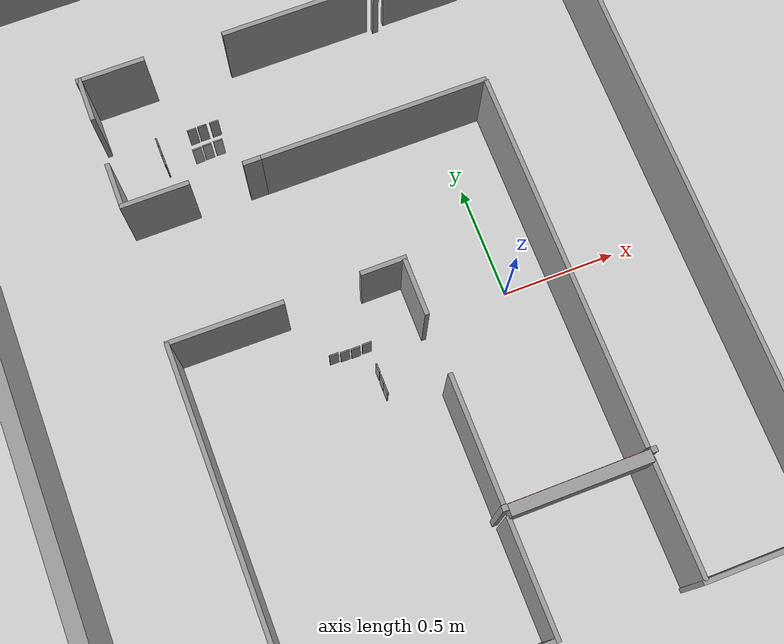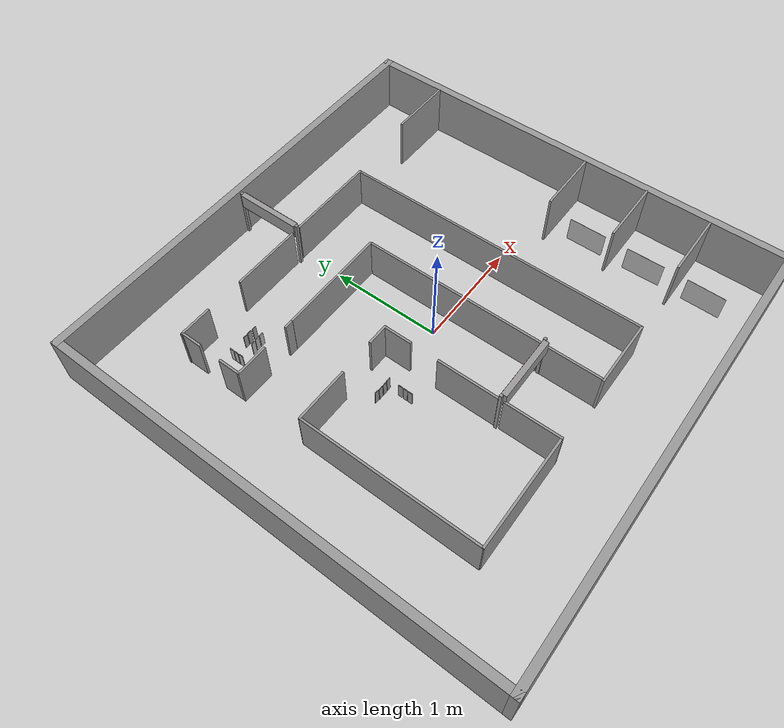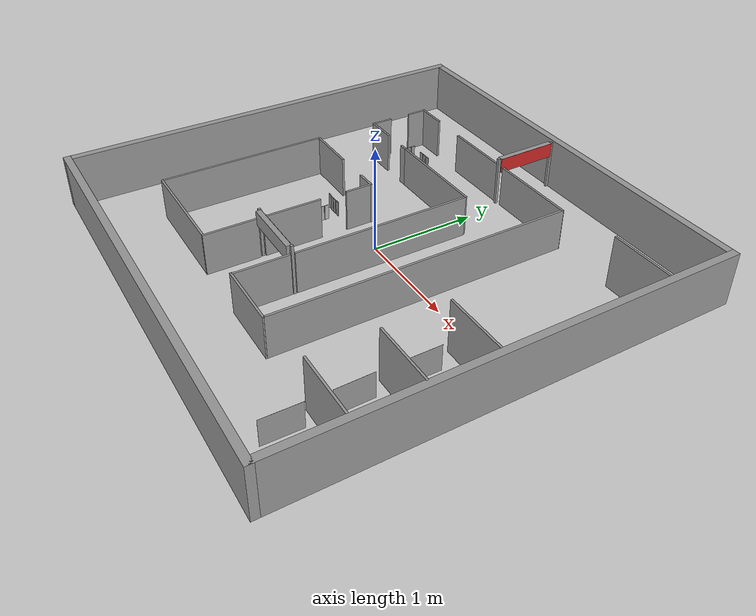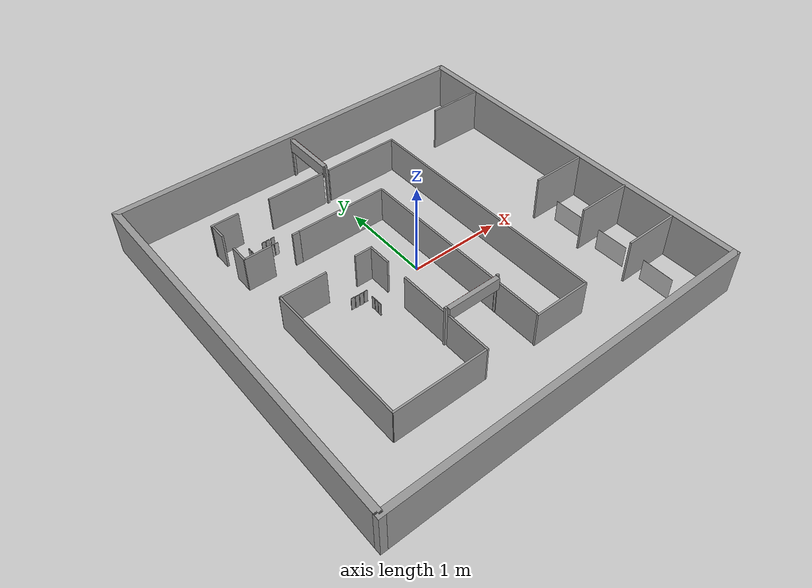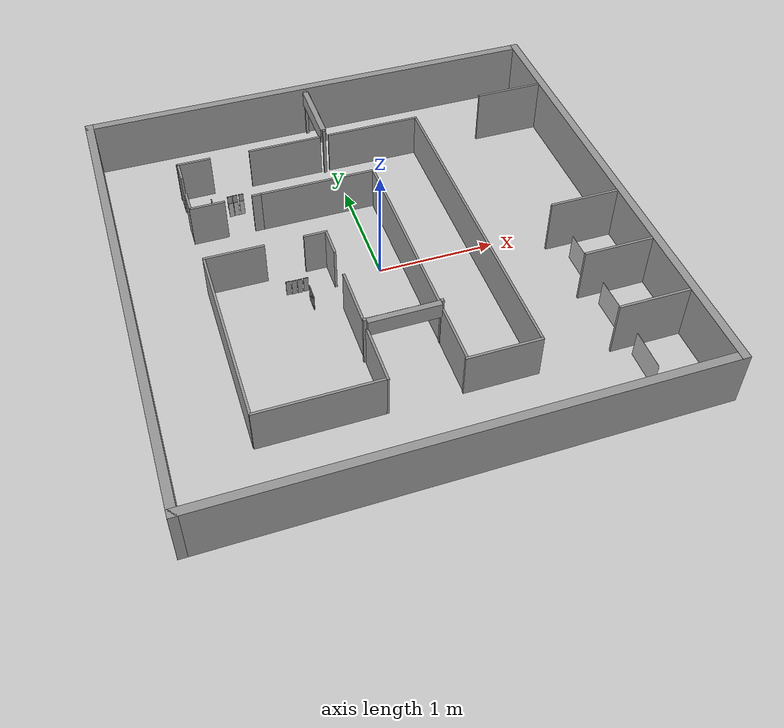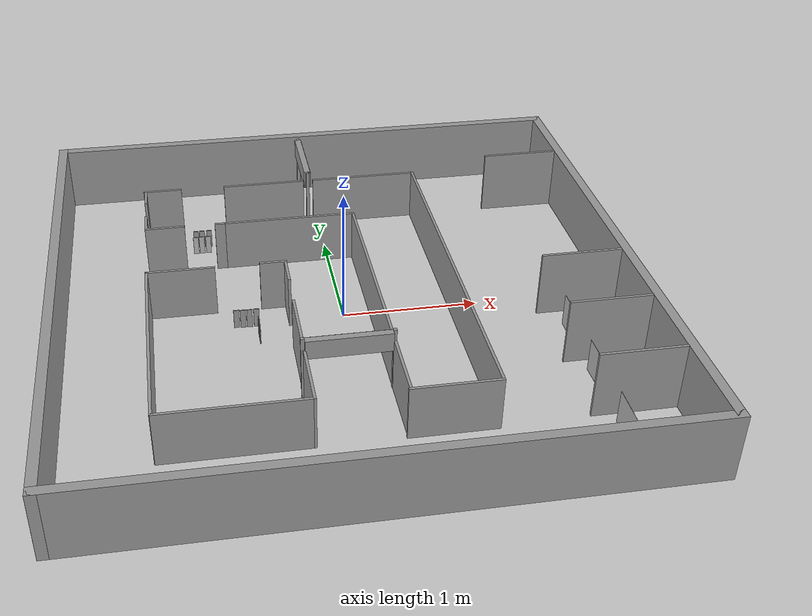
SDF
<sdf version="1.7">
 <world name="default">
  <plugin name="traffic_light_sync" filename="/home/ros1/ce/devel/lib/libceshi3_traffic_light_sync.so">
   <red_seconds>10</red_seconds>
   <green_seconds>15</green_seconds>
   <yellow_seconds>5</yellow_seconds>
   <material_uri>file:///home/ros1/ce/src/ceshi3/models/traffic_light_sync/traffic_light.material</material_uri>
   <visual>ryg3::link_1::visual</visual>
   <visual>ryg3_1::link_1::visual</visual>
   <visual>ryg3_0::link_1::visual</visual>
   <visual>ryg::link_1::visual</visual>
  </plugin>
  <light name="sun" type="directional">
   <pose>0 0 10 0 -0 0</pose>
   <diffuse>0.8 0.8 0.8 1</diffuse>
   <specular>0.2 0.2 0.2 1</specular>
   <attenuation>
    <range>1000</range>
    <constant>0.9</constant>
    <linear>0.01</linear>
    <quadratic>0.001</quadratic>
   </attenuation>
   <direction>-0.5 0.1 -0.9</direction>
   <spot><inner_angle>0</inner_angle><outer_angle>0</outer_angle><falloff>0</falloff></spot>
  </light>
  <model name="ground_plane">
   <static>1</static>
   <link name="link">
    <collision name="collision">
     <geometry><plane><normal>0 0 1</normal><size>100 100</size></plane></geometry>
     <surface>
      <contact><collide_bitmask>65535</collide_bitmask></contact>
      <friction><ode><mu>100</mu><mu2>50</mu2></ode></friction>
     </surface>
    </collision>
    <visual name="visual">
     <cast_shadows>0</cast_shadows>
     <geometry><plane><normal>0 0 1</normal><size>4.2 4.2</size></plane></geometry>
     <material><script><uri>file:///home/ros1/桌面/2/png1.material</uri><name>png1</name></script></material>
    </visual>
   </link>
  </model>
  <gravity>0 0 -9.8</gravity>
  <magnetic_field>6e-06 2.3e-05 -4.2e-05</magnetic_field>
  <atmosphere type="adiabatic"/>
  <physics type="ode">
   <max_step_size>0.001</max_step_size>
   <real_time_factor>1</real_time_factor>
   <real_time_update_rate>1000</real_time_update_rate>
  </physics>
  <scene><ambient>0.4 0.4 0.4 1</ambient><background>0.7 0.7 0.7 1</background><shadows>1</shadows></scene>
  <spherical_coordinates>
   <surface_model>EARTH_WGS84</surface_model>
   <latitude_deg>0</latitude_deg>
   <longitude_deg>0</longitude_deg>
   <elevation>0</elevation>
   <heading_deg>0</heading_deg>
  </spherical_coordinates>
  <model name="car1">
   <link name="link_0">
    <inertial>
     <mass>1</mass>
     <inertia>
      <ixx>0.166667</ixx>
      <ixy>0</ixy>
      <ixz>0</ixz>
      <iyy>0.166667</iyy>
      <iyz>0</iyz>
      <izz>0.166667</izz>
     </inertia>
    </inertial>
    <pose>0 -0.000125 -0 0 -0 0</pose>
    <visual name="visual">
     <geometry><box><size>0.345 0.0004 0.25</size></box></geometry>
     <material>
      <lighting>1</lighting>
      <script><uri>file://media/materials/scripts/gazebo.material</uri><name>Gazebo/Grey</name></script>
      <shader type="pixel"><normal_map>__default__</normal_map></shader>
      <ambient>0.3 0.3 0.3 1</ambient>
      <diffuse>0.7 0.7 0.7 1</diffuse>
      <specular>0.01 0.01 0.01 1</specular>
      <emissive>0 0 0 1</emissive>
     </material>
    </visual>
    <collision name="collision">
     <geometry><box><size>0.345 0.0004 0.25</size></box></geometry>
     <surface>
      <friction>
       <ode><mu>1</mu><mu2>1</mu2><fdir1>0 0 0</fdir1><slip1>0</slip1><slip2>0</slip2></ode>
       <torsional>
        <coefficient>1</coefficient>
        <patch_radius>0</patch_radius>
        <surface_radius>0</surface_radius>
        <use_patch_radius>1</use_patch_radius>
        <ode><slip>0</slip></ode>
       </torsional>
      </friction>
      <bounce><restitution_coefficient>0</restitution_coefficient><threshold>1e+06</threshold></bounce>
      <contact>
       <collide_without_contact>0</collide_without_contact>
       <collide_without_contact_bitmask>1</collide_without_contact_bitmask>
       <collide_bitmask>1</collide_bitmask>
       <ode>
        <soft_cfm>0</soft_cfm>
        <soft_erp>0.2</soft_erp>
        <kp>1e+13</kp>
        <kd>1</kd>
        <max_vel>0.01</max_vel>
        <min_depth>0</min_depth>
       </ode>
       <bullet>
        <split_impulse>1</split_impulse>
        <split_impulse_penetration_threshold>-0.01</split_impulse_penetration_threshold>
        <soft_cfm>0</soft_cfm>
        <soft_erp>0.2</soft_erp>
        <kp>1e+13</kp>
        <kd>1</kd>
       </bullet>
      </contact>
     </surface>
    </collision>
   </link>
   <link name="link_1">
    <inertial>
     <mass>1</mass>
     <inertia>
      <ixx>0.166667</ixx>
      <ixy>0</ixy>
      <ixz>0</ixz>
      <iyy>0.166667</iyy>
      <iyz>0</iyz>
      <izz>0.166667</izz>
     </inertia>
    </inertial>
    <pose>0 0.000125 -0 0 -0 0</pose>
    <visual name="visual">
     <geometry><box><size>0.345 0.0001 0.25</size></box></geometry>
     <material>
      <lighting>1</lighting>
      <script><uri>file:///home/ros1/model_editor_models/car1/car1.material</uri><name>car1</name></script>
     </material>
    </visual>
    <collision name="collision">
     <geometry><box><size>0.345 0.0001 0.25</size></box></geometry>
     <surface>
      <friction>
       <ode><mu>1</mu><mu2>1</mu2><fdir1>0 0 0</fdir1><slip1>0</slip1><slip2>0</slip2></ode>
       <torsional>
        <coefficient>1</coefficient>
        <patch_radius>0</patch_radius>
        <surface_radius>0</surface_radius>
        <use_patch_radius>1</use_patch_radius>
        <ode><slip>0</slip></ode>
       </torsional>
      </friction>
      <bounce><restitution_coefficient>0</restitution_coefficient><threshold>1e+06</threshold></bounce>
      <contact>
       <collide_without_contact>0</collide_without_contact>
       <collide_without_contact_bitmask>1</collide_without_contact_bitmask>
       <collide_bitmask>1</collide_bitmask>
       <ode>
        <soft_cfm>0</soft_cfm>
        <soft_erp>0.2</soft_erp>
        <kp>1e+13</kp>
        <kd>1</kd>
        <max_vel>0.01</max_vel>
        <min_depth>0</min_depth>
       </ode>
       <bullet>
        <split_impulse>1</split_impulse>
        <split_impulse_penetration_threshold>-0.01</split_impulse_penetration_threshold>
        <soft_cfm>0</soft_cfm>
        <soft_erp>0.2</soft_erp>
        <kp>1e+13</kp>
        <kd>1</kd>
       </bullet>
      </contact>
     </surface>
    </collision>
   </link>
   <static>0</static>
   <pose>1.56151 -1.63759 0.125 0 -0 1.55632</pose>
  </model>
  <model name="car1_0">
   <link name="link_0">
    <inertial>
     <mass>1</mass>
     <inertia>
      <ixx>0.166667</ixx>
      <ixy>0</ixy>
      <ixz>0</ixz>
      <iyy>0.166667</iyy>
      <iyz>0</iyz>
      <izz>0.166667</izz>
     </inertia>
    </inertial>
    <pose>0 -0.000125 -0 0 -0 0</pose>
    <visual name="visual">
     <geometry><box><size>0.345 0.0004 0.25</size></box></geometry>
     <material>
      <lighting>1</lighting>
      <script><uri>file://media/materials/scripts/gazebo.material</uri><name>Gazebo/Grey</name></script>
      <shader type="pixel"><normal_map>__default__</normal_map></shader>
      <ambient>0.3 0.3 0.3 1</ambient>
      <diffuse>0.7 0.7 0.7 1</diffuse>
      <specular>0.01 0.01 0.01 1</specular>
      <emissive>0 0 0 1</emissive>
     </material>
    </visual>
    <collision name="collision">
     <geometry><box><size>0.345 0.0004 0.25</size></box></geometry>
     <surface>
      <friction>
       <ode><mu>1</mu><mu2>1</mu2><fdir1>0 0 0</fdir1><slip1>0</slip1><slip2>0</slip2></ode>
       <torsional>
        <coefficient>1</coefficient>
        <patch_radius>0</patch_radius>
        <surface_radius>0</surface_radius>
        <use_patch_radius>1</use_patch_radius>
        <ode><slip>0</slip></ode>
       </torsional>
      </friction>
      <bounce><restitution_coefficient>0</restitution_coefficient><threshold>1e+06</threshold></bounce>
      <contact>
       <collide_without_contact>0</collide_without_contact>
       <collide_without_contact_bitmask>1</collide_without_contact_bitmask>
       <collide_bitmask>1</collide_bitmask>
       <ode>
        <soft_cfm>0</soft_cfm>
        <soft_erp>0.2</soft_erp>
        <kp>1e+13</kp>
        <kd>1</kd>
        <max_vel>0.01</max_vel>
        <min_depth>0</min_depth>
       </ode>
       <bullet>
        <split_impulse>1</split_impulse>
        <split_impulse_penetration_threshold>-0.01</split_impulse_penetration_threshold>
        <soft_cfm>0</soft_cfm>
        <soft_erp>0.2</soft_erp>
        <kp>1e+13</kp>
        <kd>1</kd>
       </bullet>
      </contact>
     </surface>
    </collision>
   </link>
   <link name="link_1">
    <inertial>
     <mass>1</mass>
     <inertia>
      <ixx>0.166667</ixx>
      <ixy>0</ixy>
      <ixz>0</ixz>
      <iyy>0.166667</iyy>
      <iyz>0</iyz>
      <izz>0.166667</izz>
     </inertia>
    </inertial>
    <pose>0 0.000125 -0 0 -0 0</pose>
    <visual name="visual">
     <geometry><box><size>0.345 0.0001 0.25</size></box></geometry>
     <material>
      <lighting>1</lighting>
      <script><uri>file:///home/ros1/model_editor_models/car2/car2.material</uri><name>car2</name></script>
     </material>
    </visual>
    <collision name="collision">
     <geometry><box><size>0.345 0.0001 0.25</size></box></geometry>
     <surface>
      <friction>
       <ode><mu>1</mu><mu2>1</mu2><fdir1>0 0 0</fdir1><slip1>0</slip1><slip2>0</slip2></ode>
       <torsional>
        <coefficient>1</coefficient>
        <patch_radius>0</patch_radius>
        <surface_radius>0</surface_radius>
        <use_patch_radius>1</use_patch_radius>
        <ode><slip>0</slip></ode>
       </torsional>
      </friction>
      <bounce><restitution_coefficient>0</restitution_coefficient><threshold>1e+06</threshold></bounce>
      <contact>
       <collide_without_contact>0</collide_without_contact>
       <collide_without_contact_bitmask>1</collide_without_contact_bitmask>
       <collide_bitmask>1</collide_bitmask>
       <ode>
        <soft_cfm>0</soft_cfm>
        <soft_erp>0.2</soft_erp>
        <kp>1e+13</kp>
        <kd>1</kd>
        <max_vel>0.01</max_vel>
        <min_depth>0</min_depth>
       </ode>
       <bullet>
        <split_impulse>1</split_impulse>
        <split_impulse_penetration_threshold>-0.01</split_impulse_penetration_threshold>
        <soft_cfm>0</soft_cfm>
        <soft_erp>0.2</soft_erp>
        <kp>1e+13</kp>
        <kd>1</kd>
       </bullet>
      </contact>
     </surface>
    </collision>
   </link>
   <static>0</static>
   <pose>1.56241 -1.07814 0.125 -3e-06 -0 1.5863</pose>
  </model>
  <model name="car1_1">
   <link name="link_0">
    <inertial>
     <mass>1</mass>
     <inertia>
      <ixx>0.166667</ixx>
      <ixy>0</ixy>
      <ixz>0</ixz>
      <iyy>0.166667</iyy>
      <iyz>0</iyz>
      <izz>0.166667</izz>
     </inertia>
    </inertial>
    <pose>0 -0.000125 -0 0 -0 0</pose>
    <visual name="visual">
     <geometry><box><size>0.345 0.0004 0.25</size></box></geometry>
     <material>
      <lighting>1</lighting>
      <script><uri>file://media/materials/scripts/gazebo.material</uri><name>Gazebo/Grey</name></script>
      <shader type="pixel"><normal_map>__default__</normal_map></shader>
      <ambient>0.3 0.3 0.3 1</ambient>
      <diffuse>0.7 0.7 0.7 1</diffuse>
      <specular>0.01 0.01 0.01 1</specular>
      <emissive>0 0 0 1</emissive>
     </material>
    </visual>
    <collision name="collision">
     <geometry><box><size>0.345 0.0004 0.25</size></box></geometry>
     <surface>
      <friction>
       <ode><mu>1</mu><mu2>1</mu2><fdir1>0 0 0</fdir1><slip1>0</slip1><slip2>0</slip2></ode>
       <torsional>
        <coefficient>1</coefficient>
        <patch_radius>0</patch_radius>
        <surface_radius>0</surface_radius>
        <use_patch_radius>1</use_patch_radius>
        <ode><slip>0</slip></ode>
       </torsional>
      </friction>
      <bounce><restitution_coefficient>0</restitution_coefficient><threshold>1e+06</threshold></bounce>
      <contact>
       <collide_without_contact>0</collide_without_contact>
       <collide_without_contact_bitmask>1</collide_without_contact_bitmask>
       <collide_bitmask>1</collide_bitmask>
       <ode>
        <soft_cfm>0</soft_cfm>
        <soft_erp>0.2</soft_erp>
        <kp>1e+13</kp>
        <kd>1</kd>
        <max_vel>0.01</max_vel>
        <min_depth>0</min_depth>
       </ode>
       <bullet>
        <split_impulse>1</split_impulse>
        <split_impulse_penetration_threshold>-0.01</split_impulse_penetration_threshold>
        <soft_cfm>0</soft_cfm>
        <soft_erp>0.2</soft_erp>
        <kp>1e+13</kp>
        <kd>1</kd>
       </bullet>
      </contact>
     </surface>
    </collision>
   </link>
   <link name="link_1">
    <inertial>
     <mass>1</mass>
     <inertia>
      <ixx>0.166667</ixx>
      <ixy>0</ixy>
      <ixz>0</ixz>
      <iyy>0.166667</iyy>
      <iyz>0</iyz>
      <izz>0.166667</izz>
     </inertia>
    </inertial>
    <pose>0 0.000125 -0 0 -0 0</pose>
    <visual name="visual">
     <geometry><box><size>0.345 0.0001 0.25</size></box></geometry>
     <material>
      <lighting>1</lighting>
      <script><uri>file:///home/ros1/model_editor_models/car3/car3.material</uri><name>car3</name></script>
     </material>
    </visual>
    <collision name="collision">
     <geometry><box><size>0.345 0.0001 0.25</size></box></geometry>
     <surface>
      <friction>
       <ode><mu>1</mu><mu2>1</mu2><fdir1>0 0 0</fdir1><slip1>0</slip1><slip2>0</slip2></ode>
       <torsional>
        <coefficient>1</coefficient>
        <patch_radius>0</patch_radius>
        <surface_radius>0</surface_radius>
        <use_patch_radius>1</use_patch_radius>
        <ode><slip>0</slip></ode>
       </torsional>
      </friction>
      <bounce><restitution_coefficient>0</restitution_coefficient><threshold>1e+06</threshold></bounce>
      <contact>
       <collide_without_contact>0</collide_without_contact>
       <collide_without_contact_bitmask>1</collide_without_contact_bitmask>
       <collide_bitmask>1</collide_bitmask>
       <ode>
        <soft_cfm>0</soft_cfm>
        <soft_erp>0.2</soft_erp>
        <kp>1e+13</kp>
        <kd>1</kd>
        <max_vel>0.01</max_vel>
        <min_depth>0</min_depth>
       </ode>
       <bullet>
        <split_impulse>1</split_impulse>
        <split_impulse_penetration_threshold>-0.01</split_impulse_penetration_threshold>
        <soft_cfm>0</soft_cfm>
        <soft_erp>0.2</soft_erp>
        <kp>1e+13</kp>
        <kd>1</kd>
       </bullet>
      </contact>
     </surface>
    </collision>
   </link>
   <static>0</static>
   <pose>1.56249 -0.521606 0.124999 0 -4e-06 1.5704</pose>
  </model>
  <model name="F1">
   <link name="link_0">
    <inertial>
     <mass>1</mass>
     <inertia>
      <ixx>0.166667</ixx>
      <ixy>0</ixy>
      <ixz>0</ixz>
      <iyy>0.166667</iyy>
      <iyz>0</iyz>
      <izz>0.166667</izz>
     </inertia>
    </inertial>
    <pose>0 -0.0015 -0 0 -0 0</pose>
    <visual name="visual">
     <geometry><box><size>0.04 0.005 0.15</size></box></geometry>
     <material>
      <lighting>1</lighting>
      <script><uri>file://media/materials/scripts/gazebo.material</uri><name>Gazebo/Grey</name></script>
      <shader type="pixel"><normal_map>__default__</normal_map></shader>
      <ambient>0.3 0.3 0.3 1</ambient>
      <diffuse>0.7 0.7 0.7 1</diffuse>
      <specular>0.01 0.01 0.01 1</specular>
      <emissive>0 0 0 1</emissive>
     </material>
    </visual>
    <collision name="collision">
     <geometry><box><size>0.04 0.005 0.15</size></box></geometry>
     <surface>
      <friction>
       <ode><mu>1</mu><mu2>1</mu2><fdir1>0 0 0</fdir1><slip1>0</slip1><slip2>0</slip2></ode>
       <torsional>
        <coefficient>1</coefficient>
        <patch_radius>0</patch_radius>
        <surface_radius>0</surface_radius>
        <use_patch_radius>1</use_patch_radius>
        <ode><slip>0</slip></ode>
       </torsional>
      </friction>
      <bounce><restitution_coefficient>0</restitution_coefficient><threshold>1e+06</threshold></bounce>
      <contact>
       <collide_without_contact>0</collide_without_contact>
       <collide_without_contact_bitmask>1</collide_without_contact_bitmask>
       <collide_bitmask>1</collide_bitmask>
       <ode>
        <soft_cfm>0</soft_cfm>
        <soft_erp>0.2</soft_erp>
        <kp>1e+13</kp>
        <kd>1</kd>
        <max_vel>0.01</max_vel>
        <min_depth>0</min_depth>
       </ode>
       <bullet>
        <split_impulse>1</split_impulse>
        <split_impulse_penetration_threshold>-0.01</split_impulse_penetration_threshold>
        <soft_cfm>0</soft_cfm>
        <soft_erp>0.2</soft_erp>
        <kp>1e+13</kp>
        <kd>1</kd>
       </bullet>
      </contact>
     </surface>
    </collision>
   </link>
   <link name="link_4">
    <inertial>
     <mass>1</mass>
     <inertia>
      <ixx>0.166667</ixx>
      <ixy>0</ixy>
      <ixz>0</ixz>
      <iyy>0.166667</iyy>
      <iyz>0</iyz>
      <izz>0.166667</izz>
     </inertia>
    </inertial>
    <pose>0 0.0015 -0 0 -0 0</pose>
    <visual name="visual">
     <geometry><box><size>0.04 0.001 0.15</size></box></geometry>
     <material>
      <script><uri>file:///home/ros1/model_editor_models/F1/F1.material</uri><name>F1</name></script>
     </material>
    </visual>
    <collision name="collision">
     <geometry><box><size>0.04 0.001 0.15</size></box></geometry>
     <surface>
      <friction>
       <ode><mu>1</mu><mu2>1</mu2><fdir1>0 0 0</fdir1><slip1>0</slip1><slip2>0</slip2></ode>
       <torsional>
        <coefficient>1</coefficient>
        <patch_radius>0</patch_radius>
        <surface_radius>0</surface_radius>
        <use_patch_radius>1</use_patch_radius>
        <ode><slip>0</slip></ode>
       </torsional>
      </friction>
      <bounce><restitution_coefficient>0</restitution_coefficient><threshold>1e+06</threshold></bounce>
      <contact>
       <collide_without_contact>0</collide_without_contact>
       <collide_without_contact_bitmask>1</collide_without_contact_bitmask>
       <collide_bitmask>1</collide_bitmask>
       <ode>
        <soft_cfm>0</soft_cfm>
        <soft_erp>0.2</soft_erp>
        <kp>1e+13</kp>
        <kd>1</kd>
        <max_vel>0.01</max_vel>
        <min_depth>0</min_depth>
       </ode>
       <bullet>
        <split_impulse>1</split_impulse>
        <split_impulse_penetration_threshold>-0.01</split_impulse_penetration_threshold>
        <soft_cfm>0</soft_cfm>
        <soft_erp>0.2</soft_erp>
        <kp>1e+13</kp>
        <kd>1</kd>
       </bullet>
      </contact>
     </surface>
    </collision>
   </link>
   <static>0</static>
   <pose>-0.916044 1.13743 0.07499 -3e-06 -3e-06 -4.1e-05</pose>
  </model>
  <model name="man-4">
   <link name="link_0">
    <inertial>
     <mass>1</mass>
     <inertia>
      <ixx>0.166667</ixx>
      <ixy>0</ixy>
      <ixz>0</ixz>
      <iyy>0.166667</iyy>
      <iyz>0</iyz>
      <izz>0.166667</izz>
     </inertia>
    </inertial>
    <pose>0 -0.0015 -0 0 -0 0</pose>
    <visual name="visual">
     <geometry><box><size>0.04 0.005 0.15</size></box></geometry>
     <material>
      <lighting>1</lighting>
      <script><uri>file://media/materials/scripts/gazebo.material</uri><name>Gazebo/Grey</name></script>
      <shader type="pixel"><normal_map>__default__</normal_map></shader>
      <ambient>0.3 0.3 0.3 1</ambient>
      <diffuse>0.7 0.7 0.7 1</diffuse>
      <specular>0.01 0.01 0.01 1</specular>
      <emissive>0 0 0 1</emissive>
     </material>
    </visual>
    <collision name="collision">
     <geometry><box><size>0.04 0.005 0.15</size></box></geometry>
     <surface>
      <friction>
       <ode><mu>1</mu><mu2>1</mu2><fdir1>0 0 0</fdir1><slip1>0</slip1><slip2>0</slip2></ode>
       <torsional>
        <coefficient>1</coefficient>
        <patch_radius>0</patch_radius>
        <surface_radius>0</surface_radius>
        <use_patch_radius>1</use_patch_radius>
        <ode><slip>0</slip></ode>
       </torsional>
      </friction>
      <bounce><restitution_coefficient>0</restitution_coefficient><threshold>1e+06</threshold></bounce>
      <contact>
       <collide_without_contact>0</collide_without_contact>
       <collide_without_contact_bitmask>1</collide_without_contact_bitmask>
       <collide_bitmask>1</collide_bitmask>
       <ode>
        <soft_cfm>0</soft_cfm>
        <soft_erp>0.2</soft_erp>
        <kp>1e+13</kp>
        <kd>1</kd>
        <max_vel>0.01</max_vel>
        <min_depth>0</min_depth>
       </ode>
       <bullet>
        <split_impulse>1</split_impulse>
        <split_impulse_penetration_threshold>-0.01</split_impulse_penetration_threshold>
        <soft_cfm>0</soft_cfm>
        <soft_erp>0.2</soft_erp>
        <kp>1e+13</kp>
        <kd>1</kd>
       </bullet>
      </contact>
     </surface>
    </collision>
   </link>
   <link name="link_4">
    <inertial>
     <mass>1</mass>
     <inertia>
      <ixx>0.166667</ixx>
      <ixy>0</ixy>
      <ixz>0</ixz>
      <iyy>0.166667</iyy>
      <iyz>0</iyz>
      <izz>0.166667</izz>
     </inertia>
    </inertial>
    <pose>0 0.0015 -0 0 -0 0</pose>
    <visual name="visual">
     <geometry><box><size>0.04 0.001 0.15</size></box></geometry>
     <material>
      <script><uri>file:///home/ros1/model_editor_models/man-4/man_4.material</uri><name>man_4</name></script>
     </material>
    </visual>
    <collision name="collision">
     <geometry><box><size>0.04 0.001 0.15</size></box></geometry>
     <surface>
      <friction>
       <ode><mu>1</mu><mu2>1</mu2><fdir1>0 0 0</fdir1><slip1>0</slip1><slip2>0</slip2></ode>
       <torsional>
        <coefficient>1</coefficient>
        <patch_radius>0</patch_radius>
        <surface_radius>0</surface_radius>
        <use_patch_radius>1</use_patch_radius>
        <ode><slip>0</slip></ode>
       </torsional>
      </friction>
      <bounce><restitution_coefficient>0</restitution_coefficient><threshold>1e+06</threshold></bounce>
      <contact>
       <collide_without_contact>0</collide_without_contact>
       <collide_without_contact_bitmask>1</collide_without_contact_bitmask>
       <collide_bitmask>1</collide_bitmask>
       <ode>
        <soft_cfm>0</soft_cfm>
        <soft_erp>0.2</soft_erp>
        <kp>1e+13</kp>
        <kd>1</kd>
        <max_vel>0.01</max_vel>
        <min_depth>0</min_depth>
       </ode>
       <bullet>
        <split_impulse>1</split_impulse>
        <split_impulse_penetration_threshold>-0.01</split_impulse_penetration_threshold>
        <soft_cfm>0</soft_cfm>
        <soft_erp>0.2</soft_erp>
        <kp>1e+13</kp>
        <kd>1</kd>
       </bullet>
      </contact>
     </surface>
    </collision>
   </link>
   <static>0</static>
   <pose>-1.17659 1.08772 0.075 -1.1e-05 1.8e-05 1.54319</pose>
  </model>
  <model name="man-5">
   <link name="link_0">
    <inertial>
     <mass>1</mass>
     <inertia>
      <ixx>0.166667</ixx>
      <ixy>0</ixy>
      <ixz>0</ixz>
      <iyy>0.166667</iyy>
      <iyz>0</iyz>
      <izz>0.166667</izz>
     </inertia>
    </inertial>
    <pose>0 -0.0015 -0 0 -0 0</pose>
    <visual name="visual">
     <geometry><box><size>0.04 0.005 0.15</size></box></geometry>
     <material>
      <lighting>1</lighting>
      <script><uri>file://media/materials/scripts/gazebo.material</uri><name>Gazebo/Grey</name></script>
      <shader type="pixel"><normal_map>__default__</normal_map></shader>
      <ambient>0.3 0.3 0.3 1</ambient>
      <diffuse>0.7 0.7 0.7 1</diffuse>
      <specular>0.01 0.01 0.01 1</specular>
      <emissive>0 0 0 1</emissive>
     </material>
    </visual>
    <collision name="collision">
     <geometry><box><size>0.04 0.005 0.15</size></box></geometry>
     <surface>
      <friction>
       <ode><mu>1</mu><mu2>1</mu2><fdir1>0 0 0</fdir1><slip1>0</slip1><slip2>0</slip2></ode>
       <torsional>
        <coefficient>1</coefficient>
        <patch_radius>0</patch_radius>
        <surface_radius>0</surface_radius>
        <use_patch_radius>1</use_patch_radius>
        <ode><slip>0</slip></ode>
       </torsional>
      </friction>
      <bounce><restitution_coefficient>0</restitution_coefficient><threshold>1e+06</threshold></bounce>
      <contact>
       <collide_without_contact>0</collide_without_contact>
       <collide_without_contact_bitmask>1</collide_without_contact_bitmask>
       <collide_bitmask>1</collide_bitmask>
       <ode>
        <soft_cfm>0</soft_cfm>
        <soft_erp>0.2</soft_erp>
        <kp>1e+13</kp>
        <kd>1</kd>
        <max_vel>0.01</max_vel>
        <min_depth>0</min_depth>
       </ode>
       <bullet>
        <split_impulse>1</split_impulse>
        <split_impulse_penetration_threshold>-0.01</split_impulse_penetration_threshold>
        <soft_cfm>0</soft_cfm>
        <soft_erp>0.2</soft_erp>
        <kp>1e+13</kp>
        <kd>1</kd>
       </bullet>
      </contact>
     </surface>
    </collision>
   </link>
   <link name="link_4">
    <inertial>
     <mass>1</mass>
     <inertia>
      <ixx>0.166667</ixx>
      <ixy>0</ixy>
      <ixz>0</ixz>
      <iyy>0.166667</iyy>
      <iyz>0</iyz>
      <izz>0.166667</izz>
     </inertia>
    </inertial>
    <pose>0 0.0015 -0 0 -0 0</pose>
    <visual name="visual">
     <geometry><box><size>0.04 0.001 0.15</size></box></geometry>
     <material>
      <script><uri>file:///home/ros1/model_editor_models/man-5/man_5.material</uri><name>man_5</name></script>
     </material>
    </visual>
    <collision name="collision">
     <geometry><box><size>0.04 0.001 0.15</size></box></geometry>
     <surface>
      <friction>
       <ode><mu>1</mu><mu2>1</mu2><fdir1>0 0 0</fdir1><slip1>0</slip1><slip2>0</slip2></ode>
       <torsional>
        <coefficient>1</coefficient>
        <patch_radius>0</patch_radius>
        <surface_radius>0</surface_radius>
        <use_patch_radius>1</use_patch_radius>
        <ode><slip>0</slip></ode>
       </torsional>
      </friction>
      <bounce><restitution_coefficient>0</restitution_coefficient><threshold>1e+06</threshold></bounce>
      <contact>
       <collide_without_contact>0</collide_without_contact>
       <collide_without_contact_bitmask>1</collide_without_contact_bitmask>
       <collide_bitmask>1</collide_bitmask>
       <ode>
        <soft_cfm>0</soft_cfm>
        <soft_erp>0.2</soft_erp>
        <kp>1e+13</kp>
        <kd>1</kd>
        <max_vel>0.01</max_vel>
        <min_depth>0</min_depth>
       </ode>
       <bullet>
        <split_impulse>1</split_impulse>
        <split_impulse_penetration_threshold>-0.01</split_impulse_penetration_threshold>
        <soft_cfm>0</soft_cfm>
        <soft_erp>0.2</soft_erp>
        <kp>1e+13</kp>
        <kd>1</kd>
       </bullet>
      </contact>
     </surface>
    </collision>
   </link>
   <static>0</static>
   <pose>-1.17679 1.1326 0.075 -6e-06 6e-06 1.56191</pose>
  </model>
  <model name="man-6">
   <link name="link_0">
    <inertial>
     <mass>1</mass>
     <inertia>
      <ixx>0.166667</ixx>
      <ixy>0</ixy>
      <ixz>0</ixz>
      <iyy>0.166667</iyy>
      <iyz>0</iyz>
      <izz>0.166667</izz>
     </inertia>
    </inertial>
    <pose>0 -0.0015 -0 0 -0 0</pose>
    <visual name="visual">
     <geometry><box><size>0.04 0.005 0.15</size></box></geometry>
     <material>
      <lighting>1</lighting>
      <script><uri>file://media/materials/scripts/gazebo.material</uri><name>Gazebo/Grey</name></script>
      <shader type="pixel"><normal_map>__default__</normal_map></shader>
      <ambient>0.3 0.3 0.3 1</ambient>
      <diffuse>0.7 0.7 0.7 1</diffuse>
      <specular>0.01 0.01 0.01 1</specular>
      <emissive>0 0 0 1</emissive>
     </material>
    </visual>
    <collision name="collision">
     <geometry><box><size>0.04 0.005 0.15</size></box></geometry>
     <surface>
      <friction>
       <ode><mu>1</mu><mu2>1</mu2><fdir1>0 0 0</fdir1><slip1>0</slip1><slip2>0</slip2></ode>
       <torsional>
        <coefficient>1</coefficient>
        <patch_radius>0</patch_radius>
        <surface_radius>0</surface_radius>
        <use_patch_radius>1</use_patch_radius>
        <ode><slip>0</slip></ode>
       </torsional>
      </friction>
      <bounce><restitution_coefficient>0</restitution_coefficient><threshold>1e+06</threshold></bounce>
      <contact>
       <collide_without_contact>0</collide_without_contact>
       <collide_without_contact_bitmask>1</collide_without_contact_bitmask>
       <collide_bitmask>1</collide_bitmask>
       <ode>
        <soft_cfm>0</soft_cfm>
        <soft_erp>0.2</soft_erp>
        <kp>1e+13</kp>
        <kd>1</kd>
        <max_vel>0.01</max_vel>
        <min_depth>0</min_depth>
       </ode>
       <bullet>
        <split_impulse>1</split_impulse>
        <split_impulse_penetration_threshold>-0.01</split_impulse_penetration_threshold>
        <soft_cfm>0</soft_cfm>
        <soft_erp>0.2</soft_erp>
        <kp>1e+13</kp>
        <kd>1</kd>
       </bullet>
      </contact>
     </surface>
    </collision>
   </link>
   <link name="link_4">
    <inertial>
     <mass>1</mass>
     <inertia>
      <ixx>0.166667</ixx>
      <ixy>0</ixy>
      <ixz>0</ixz>
      <iyy>0.166667</iyy>
      <iyz>0</iyz>
      <izz>0.166667</izz>
     </inertia>
    </inertial>
    <pose>0 0.0015 -0 0 -0 0</pose>
    <visual name="visual">
     <geometry><box><size>0.04 0.001 0.15</size></box></geometry>
     <material>
      <script><uri>file:///home/ros1/model_editor_models/man-6/man_6.material</uri><name>man_6</name></script>
     </material>
    </visual>
    <collision name="collision">
     <geometry><box><size>0.04 0.001 0.15</size></box></geometry>
     <surface>
      <friction>
       <ode><mu>1</mu><mu2>1</mu2><fdir1>0 0 0</fdir1><slip1>0</slip1><slip2>0</slip2></ode>
       <torsional>
        <coefficient>1</coefficient>
        <patch_radius>0</patch_radius>
        <surface_radius>0</surface_radius>
        <use_patch_radius>1</use_patch_radius>
        <ode><slip>0</slip></ode>
       </torsional>
      </friction>
      <bounce><restitution_coefficient>0</restitution_coefficient><threshold>1e+06</threshold></bounce>
      <contact>
       <collide_without_contact>0</collide_without_contact>
       <collide_without_contact_bitmask>1</collide_without_contact_bitmask>
       <collide_bitmask>1</collide_bitmask>
       <ode>
        <soft_cfm>0</soft_cfm>
        <soft_erp>0.2</soft_erp>
        <kp>1e+13</kp>
        <kd>1</kd>
        <max_vel>0.01</max_vel>
        <min_depth>0</min_depth>
       </ode>
       <bullet>
        <split_impulse>1</split_impulse>
        <split_impulse_penetration_threshold>-0.01</split_impulse_penetration_threshold>
        <soft_cfm>0</soft_cfm>
        <soft_erp>0.2</soft_erp>
        <kp>1e+13</kp>
        <kd>1</kd>
       </bullet>
      </contact>
     </surface>
    </collision>
   </link>
   <static>0</static>
   <pose>-1.02579 1.04198 0.075 -9e-06 7e-06 -3.09878</pose>
  </model>
  <model name="man-7">
   <link name="link_0">
    <inertial>
     <mass>1</mass>
     <inertia>
      <ixx>0.166667</ixx>
      <ixy>0</ixy>
      <ixz>0</ixz>
      <iyy>0.166667</iyy>
      <iyz>0</iyz>
      <izz>0.166667</izz>
     </inertia>
    </inertial>
    <pose>0 -0.0015 -0 0 -0 0</pose>
    <visual name="visual">
     <geometry><box><size>0.04 0.005 0.15</size></box></geometry>
     <material>
      <lighting>1</lighting>
      <script><uri>file://media/materials/scripts/gazebo.material</uri><name>Gazebo/Grey</name></script>
      <shader type="pixel"><normal_map>__default__</normal_map></shader>
      <ambient>0.3 0.3 0.3 1</ambient>
      <diffuse>0.7 0.7 0.7 1</diffuse>
      <specular>0.01 0.01 0.01 1</specular>
      <emissive>0 0 0 1</emissive>
     </material>
    </visual>
    <collision name="collision">
     <geometry><box><size>0.04 0.005 0.15</size></box></geometry>
     <surface>
      <friction>
       <ode><mu>1</mu><mu2>1</mu2><fdir1>0 0 0</fdir1><slip1>0</slip1><slip2>0</slip2></ode>
       <torsional>
        <coefficient>1</coefficient>
        <patch_radius>0</patch_radius>
        <surface_radius>0</surface_radius>
        <use_patch_radius>1</use_patch_radius>
        <ode><slip>0</slip></ode>
       </torsional>
      </friction>
      <bounce><restitution_coefficient>0</restitution_coefficient><threshold>1e+06</threshold></bounce>
      <contact>
       <collide_without_contact>0</collide_without_contact>
       <collide_without_contact_bitmask>1</collide_without_contact_bitmask>
       <collide_bitmask>1</collide_bitmask>
       <ode>
        <soft_cfm>0</soft_cfm>
        <soft_erp>0.2</soft_erp>
        <kp>1e+13</kp>
        <kd>1</kd>
        <max_vel>0.01</max_vel>
        <min_depth>0</min_depth>
       </ode>
       <bullet>
        <split_impulse>1</split_impulse>
        <split_impulse_penetration_threshold>-0.01</split_impulse_penetration_threshold>
        <soft_cfm>0</soft_cfm>
        <soft_erp>0.2</soft_erp>
        <kp>1e+13</kp>
        <kd>1</kd>
       </bullet>
      </contact>
     </surface>
    </collision>
   </link>
   <link name="link_4">
    <inertial>
     <mass>1</mass>
     <inertia>
      <ixx>0.166667</ixx>
      <ixy>0</ixy>
      <ixz>0</ixz>
      <iyy>0.166667</iyy>
      <iyz>0</iyz>
      <izz>0.166667</izz>
     </inertia>
    </inertial>
    <pose>0 0.0015 -0 0 -0 0</pose>
    <visual name="visual">
     <geometry><box><size>0.04 0.001 0.15</size></box></geometry>
     <material>
      <script><uri>file:///home/ros1/model_editor_models/man-7/man_7.material</uri><name>man_7</name></script>
     </material>
    </visual>
    <collision name="collision">
     <geometry><box><size>0.04 0.001 0.15</size></box></geometry>
     <surface>
      <friction>
       <ode><mu>1</mu><mu2>1</mu2><fdir1>0 0 0</fdir1><slip1>0</slip1><slip2>0</slip2></ode>
       <torsional>
        <coefficient>1</coefficient>
        <patch_radius>0</patch_radius>
        <surface_radius>0</surface_radius>
        <use_patch_radius>1</use_patch_radius>
        <ode><slip>0</slip></ode>
       </torsional>
      </friction>
      <bounce><restitution_coefficient>0</restitution_coefficient><threshold>1e+06</threshold></bounce>
      <contact>
       <collide_without_contact>0</collide_without_contact>
       <collide_without_contact_bitmask>1</collide_without_contact_bitmask>
       <collide_bitmask>1</collide_bitmask>
       <ode>
        <soft_cfm>0</soft_cfm>
        <soft_erp>0.2</soft_erp>
        <kp>1e+13</kp>
        <kd>1</kd>
        <max_vel>0.01</max_vel>
        <min_depth>0</min_depth>
       </ode>
       <bullet>
        <split_impulse>1</split_impulse>
        <split_impulse_penetration_threshold>-0.01</split_impulse_penetration_threshold>
        <soft_cfm>0</soft_cfm>
        <soft_erp>0.2</soft_erp>
        <kp>1e+13</kp>
        <kd>1</kd>
       </bullet>
      </contact>
     </surface>
    </collision>
   </link>
   <static>0</static>
   <pose>-0.979135 1.04472 0.074991 -8e-06 2.9e-05 -3.12383</pose>
  </model>
  <model name="F2">
   <link name="link_0">
    <inertial>
     <mass>1</mass>
     <inertia>
      <ixx>0.166667</ixx>
      <ixy>0</ixy>
      <ixz>0</ixz>
      <iyy>0.166667</iyy>
      <iyz>0</iyz>
      <izz>0.166667</izz>
     </inertia>
    </inertial>
    <pose>0 -0.0015 -0 0 -0 0</pose>
    <visual name="visual">
     <geometry><box><size>0.04 0.005 0.15</size></box></geometry>
     <material>
      <lighting>1</lighting>
      <script><uri>file://media/materials/scripts/gazebo.material</uri><name>Gazebo/Grey</name></script>
      <shader type="pixel"><normal_map>__default__</normal_map></shader>
      <ambient>0.3 0.3 0.3 1</ambient>
      <diffuse>0.7 0.7 0.7 1</diffuse>
      <specular>0.01 0.01 0.01 1</specular>
      <emissive>0 0 0 1</emissive>
     </material>
    </visual>
    <collision name="collision">
     <geometry><box><size>0.04 0.005 0.15</size></box></geometry>
     <surface>
      <friction>
       <ode><mu>1</mu><mu2>1</mu2><fdir1>0 0 0</fdir1><slip1>0</slip1><slip2>0</slip2></ode>
       <torsional>
        <coefficient>1</coefficient>
        <patch_radius>0</patch_radius>
        <surface_radius>0</surface_radius>
        <use_patch_radius>1</use_patch_radius>
        <ode><slip>0</slip></ode>
       </torsional>
      </friction>
      <bounce><restitution_coefficient>0</restitution_coefficient><threshold>1e+06</threshold></bounce>
      <contact>
       <collide_without_contact>0</collide_without_contact>
       <collide_without_contact_bitmask>1</collide_without_contact_bitmask>
       <collide_bitmask>1</collide_bitmask>
       <ode>
        <soft_cfm>0</soft_cfm>
        <soft_erp>0.2</soft_erp>
        <kp>1e+13</kp>
        <kd>1</kd>
        <max_vel>0.01</max_vel>
        <min_depth>0</min_depth>
       </ode>
       <bullet>
        <split_impulse>1</split_impulse>
        <split_impulse_penetration_threshold>-0.01</split_impulse_penetration_threshold>
        <soft_cfm>0</soft_cfm>
        <soft_erp>0.2</soft_erp>
        <kp>1e+13</kp>
        <kd>1</kd>
       </bullet>
      </contact>
     </surface>
    </collision>
   </link>
   <link name="link_4">
    <inertial>
     <mass>1</mass>
     <inertia>
      <ixx>0.166667</ixx>
      <ixy>0</ixy>
      <ixz>0</ixz>
      <iyy>0.166667</iyy>
      <iyz>0</iyz>
      <izz>0.166667</izz>
     </inertia>
    </inertial>
    <pose>0 0.0015 -0 0 -0 0</pose>
    <visual name="visual">
     <geometry><box><size>0.04 0.001 0.15</size></box></geometry>
     <material>
      <script><uri>file:///home/ros1/model_editor_models/F2/F2.material</uri><name>F2</name></script>
     </material>
    </visual>
    <collision name="collision">
     <geometry><box><size>0.04 0.001 0.15</size></box></geometry>
     <surface>
      <friction>
       <ode><mu>1</mu><mu2>1</mu2><fdir1>0 0 0</fdir1><slip1>0</slip1><slip2>0</slip2></ode>
       <torsional>
        <coefficient>1</coefficient>
        <patch_radius>0</patch_radius>
        <surface_radius>0</surface_radius>
        <use_patch_radius>1</use_patch_radius>
        <ode><slip>0</slip></ode>
       </torsional>
      </friction>
      <bounce><restitution_coefficient>0</restitution_coefficient><threshold>1e+06</threshold></bounce>
      <contact>
       <collide_without_contact>0</collide_without_contact>
       <collide_without_contact_bitmask>1</collide_without_contact_bitmask>
       <collide_bitmask>1</collide_bitmask>
       <ode>
        <soft_cfm>0</soft_cfm>
        <soft_erp>0.2</soft_erp>
        <kp>1e+13</kp>
        <kd>1</kd>
        <max_vel>0.01</max_vel>
        <min_depth>0</min_depth>
       </ode>
       <bullet>
        <split_impulse>1</split_impulse>
        <split_impulse_penetration_threshold>-0.01</split_impulse_penetration_threshold>
        <soft_cfm>0</soft_cfm>
        <soft_erp>0.2</soft_erp>
        <kp>1e+13</kp>
        <kd>1</kd>
       </bullet>
      </contact>
     </surface>
    </collision>
   </link>
   <static>0</static>
   <pose>-0.928451 1.04611 0.074991 5e-06 -1.5e-05 -3.14148</pose>
  </model>
  <model name="man-8">
   <link name="link_0">
    <inertial>
     <mass>1</mass>
     <inertia>
      <ixx>0.166667</ixx>
      <ixy>0</ixy>
      <ixz>0</ixz>
      <iyy>0.166667</iyy>
      <iyz>0</iyz>
      <izz>0.166667</izz>
     </inertia>
    </inertial>
    <pose>0 -0.0015 -0 0 -0 0</pose>
    <visual name="visual">
     <geometry><box><size>0.04 0.005 0.15</size></box></geometry>
     <material>
      <lighting>1</lighting>
      <script><uri>file://media/materials/scripts/gazebo.material</uri><name>Gazebo/Grey</name></script>
      <shader type="pixel"><normal_map>__default__</normal_map></shader>
      <ambient>0.3 0.3 0.3 1</ambient>
      <diffuse>0.7 0.7 0.7 1</diffuse>
      <specular>0.01 0.01 0.01 1</specular>
      <emissive>0 0 0 1</emissive>
     </material>
    </visual>
    <collision name="collision">
     <geometry><box><size>0.04 0.005 0.15</size></box></geometry>
     <surface>
      <friction>
       <ode><mu>1</mu><mu2>1</mu2><fdir1>0 0 0</fdir1><slip1>0</slip1><slip2>0</slip2></ode>
       <torsional>
        <coefficient>1</coefficient>
        <patch_radius>0</patch_radius>
        <surface_radius>0</surface_radius>
        <use_patch_radius>1</use_patch_radius>
        <ode><slip>0</slip></ode>
       </torsional>
      </friction>
      <bounce><restitution_coefficient>0</restitution_coefficient><threshold>1e+06</threshold></bounce>
      <contact>
       <collide_without_contact>0</collide_without_contact>
       <collide_without_contact_bitmask>1</collide_without_contact_bitmask>
       <collide_bitmask>1</collide_bitmask>
       <ode>
        <soft_cfm>0</soft_cfm>
        <soft_erp>0.2</soft_erp>
        <kp>1e+13</kp>
        <kd>1</kd>
        <max_vel>0.01</max_vel>
        <min_depth>0</min_depth>
       </ode>
       <bullet>
        <split_impulse>1</split_impulse>
        <split_impulse_penetration_threshold>-0.01</split_impulse_penetration_threshold>
        <soft_cfm>0</soft_cfm>
        <soft_erp>0.2</soft_erp>
        <kp>1e+13</kp>
        <kd>1</kd>
       </bullet>
      </contact>
     </surface>
    </collision>
   </link>
   <link name="link_4">
    <inertial>
     <mass>1</mass>
     <inertia>
      <ixx>0.166667</ixx>
      <ixy>0</ixy>
      <ixz>0</ixz>
      <iyy>0.166667</iyy>
      <iyz>0</iyz>
      <izz>0.166667</izz>
     </inertia>
    </inertial>
    <pose>0 0.0015 -0 0 -0 0</pose>
    <visual name="visual">
     <geometry><box><size>0.04 0.001 0.15</size></box></geometry>
     <material>
      <script><uri>file:///home/ros1/model_editor_models/man-8/man_8.material</uri><name>man_8</name></script>
     </material>
    </visual>
    <collision name="collision">
     <geometry><box><size>0.04 0.001 0.15</size></box></geometry>
     <surface>
      <friction>
       <ode><mu>1</mu><mu2>1</mu2><fdir1>0 0 0</fdir1><slip1>0</slip1><slip2>0</slip2></ode>
       <torsional>
        <coefficient>1</coefficient>
        <patch_radius>0</patch_radius>
        <surface_radius>0</surface_radius>
        <use_patch_radius>1</use_patch_radius>
        <ode><slip>0</slip></ode>
       </torsional>
      </friction>
      <bounce><restitution_coefficient>0</restitution_coefficient><threshold>1e+06</threshold></bounce>
      <contact>
       <collide_without_contact>0</collide_without_contact>
       <collide_without_contact_bitmask>1</collide_without_contact_bitmask>
       <collide_bitmask>1</collide_bitmask>
       <ode>
        <soft_cfm>0</soft_cfm>
        <soft_erp>0.2</soft_erp>
        <kp>1e+13</kp>
        <kd>1</kd>
        <max_vel>0.01</max_vel>
        <min_depth>0</min_depth>
       </ode>
       <bullet>
        <split_impulse>1</split_impulse>
        <split_impulse_penetration_threshold>-0.01</split_impulse_penetration_threshold>
        <soft_cfm>0</soft_cfm>
        <soft_erp>0.2</soft_erp>
        <kp>1e+13</kp>
        <kd>1</kd>
       </bullet>
      </contact>
     </surface>
    </collision>
   </link>
   <static>0</static>
   <pose>-0.742893 -0.02823 0.075002 8e-06 8.7e-05 0.000148</pose>
  </model>
  <model name="man-9">
   <link name="link_0">
    <inertial>
     <mass>1</mass>
     <inertia>
      <ixx>0.166667</ixx>
      <ixy>0</ixy>
      <ixz>0</ixz>
      <iyy>0.166667</iyy>
      <iyz>0</iyz>
      <izz>0.166667</izz>
     </inertia>
    </inertial>
    <pose>0 -0.0015 -0 0 -0 0</pose>
    <visual name="visual">
     <geometry><box><size>0.04 0.005 0.15</size></box></geometry>
     <material>
      <lighting>1</lighting>
      <script><uri>file://media/materials/scripts/gazebo.material</uri><name>Gazebo/Grey</name></script>
      <shader type="pixel"><normal_map>__default__</normal_map></shader>
      <ambient>0.3 0.3 0.3 1</ambient>
      <diffuse>0.7 0.7 0.7 1</diffuse>
      <specular>0.01 0.01 0.01 1</specular>
      <emissive>0 0 0 1</emissive>
     </material>
    </visual>
    <collision name="collision">
     <geometry><box><size>0.04 0.005 0.15</size></box></geometry>
     <surface>
      <friction>
       <ode><mu>1</mu><mu2>1</mu2><fdir1>0 0 0</fdir1><slip1>0</slip1><slip2>0</slip2></ode>
       <torsional>
        <coefficient>1</coefficient>
        <patch_radius>0</patch_radius>
        <surface_radius>0</surface_radius>
        <use_patch_radius>1</use_patch_radius>
        <ode><slip>0</slip></ode>
       </torsional>
      </friction>
      <bounce><restitution_coefficient>0</restitution_coefficient><threshold>1e+06</threshold></bounce>
      <contact>
       <collide_without_contact>0</collide_without_contact>
       <collide_without_contact_bitmask>1</collide_without_contact_bitmask>
       <collide_bitmask>1</collide_bitmask>
       <ode>
        <soft_cfm>0</soft_cfm>
        <soft_erp>0.2</soft_erp>
        <kp>1e+13</kp>
        <kd>1</kd>
        <max_vel>0.01</max_vel>
        <min_depth>0</min_depth>
       </ode>
       <bullet>
        <split_impulse>1</split_impulse>
        <split_impulse_penetration_threshold>-0.01</split_impulse_penetration_threshold>
        <soft_cfm>0</soft_cfm>
        <soft_erp>0.2</soft_erp>
        <kp>1e+13</kp>
        <kd>1</kd>
       </bullet>
      </contact>
     </surface>
    </collision>
   </link>
   <link name="link_4">
    <inertial>
     <mass>1</mass>
     <inertia>
      <ixx>0.166667</ixx>
      <ixy>0</ixy>
      <ixz>0</ixz>
      <iyy>0.166667</iyy>
      <iyz>0</iyz>
      <izz>0.166667</izz>
     </inertia>
    </inertial>
    <pose>0 0.0015 -0 0 -0 0</pose>
    <visual name="visual">
     <geometry><box><size>0.04 0.001 0.15</size></box></geometry>
     <material>
      <script><uri>file:///home/ros1/model_editor_models/man-9/man_9.material</uri><name>man_9</name></script>
     </material>
    </visual>
    <collision name="collision">
     <geometry><box><size>0.04 0.001 0.15</size></box></geometry>
     <surface>
      <friction>
       <ode><mu>1</mu><mu2>1</mu2><fdir1>0 0 0</fdir1><slip1>0</slip1><slip2>0</slip2></ode>
       <torsional>
        <coefficient>1</coefficient>
        <patch_radius>0</patch_radius>
        <surface_radius>0</surface_radius>
        <use_patch_radius>1</use_patch_radius>
        <ode><slip>0</slip></ode>
       </torsional>
      </friction>
      <bounce><restitution_coefficient>0</restitution_coefficient><threshold>1e+06</threshold></bounce>
      <contact>
       <collide_without_contact>0</collide_without_contact>
       <collide_without_contact_bitmask>1</collide_without_contact_bitmask>
       <collide_bitmask>1</collide_bitmask>
       <ode>
        <soft_cfm>0</soft_cfm>
        <soft_erp>0.2</soft_erp>
        <kp>1e+13</kp>
        <kd>1</kd>
        <max_vel>0.01</max_vel>
        <min_depth>0</min_depth>
       </ode>
       <bullet>
        <split_impulse>1</split_impulse>
        <split_impulse_penetration_threshold>-0.01</split_impulse_penetration_threshold>
        <soft_cfm>0</soft_cfm>
        <soft_erp>0.2</soft_erp>
        <kp>1e+13</kp>
        <kd>1</kd>
       </bullet>
      </contact>
     </surface>
    </collision>
   </link>
   <static>0</static>
   <pose>-0.69575 -0.029877 0.075 -2e-06 -1.1e-05 -9.8e-05</pose>
  </model>
  <model name="man-10">
   <link name="link_0">
    <inertial>
     <mass>1</mass>
     <inertia>
      <ixx>0.166667</ixx>
      <ixy>0</ixy>
      <ixz>0</ixz>
      <iyy>0.166667</iyy>
      <iyz>0</iyz>
      <izz>0.166667</izz>
     </inertia>
    </inertial>
    <pose>0 -0.0015 -0 0 -0 0</pose>
    <visual name="visual">
     <geometry><box><size>0.04 0.005 0.15</size></box></geometry>
     <material>
      <lighting>1</lighting>
      <script><uri>file://media/materials/scripts/gazebo.material</uri><name>Gazebo/Grey</name></script>
      <shader type="pixel"><normal_map>__default__</normal_map></shader>
      <ambient>0.3 0.3 0.3 1</ambient>
      <diffuse>0.7 0.7 0.7 1</diffuse>
      <specular>0.01 0.01 0.01 1</specular>
      <emissive>0 0 0 1</emissive>
     </material>
    </visual>
    <collision name="collision">
     <geometry><box><size>0.04 0.005 0.15</size></box></geometry>
     <surface>
      <friction>
       <ode><mu>1</mu><mu2>1</mu2><fdir1>0 0 0</fdir1><slip1>0</slip1><slip2>0</slip2></ode>
       <torsional>
        <coefficient>1</coefficient>
        <patch_radius>0</patch_radius>
        <surface_radius>0</surface_radius>
        <use_patch_radius>1</use_patch_radius>
        <ode><slip>0</slip></ode>
       </torsional>
      </friction>
      <bounce><restitution_coefficient>0</restitution_coefficient><threshold>1e+06</threshold></bounce>
      <contact>
       <collide_without_contact>0</collide_without_contact>
       <collide_without_contact_bitmask>1</collide_without_contact_bitmask>
       <collide_bitmask>1</collide_bitmask>
       <ode>
        <soft_cfm>0</soft_cfm>
        <soft_erp>0.2</soft_erp>
        <kp>1e+13</kp>
        <kd>1</kd>
        <max_vel>0.01</max_vel>
        <min_depth>0</min_depth>
       </ode>
       <bullet>
        <split_impulse>1</split_impulse>
        <split_impulse_penetration_threshold>-0.01</split_impulse_penetration_threshold>
        <soft_cfm>0</soft_cfm>
        <soft_erp>0.2</soft_erp>
        <kp>1e+13</kp>
        <kd>1</kd>
       </bullet>
      </contact>
     </surface>
    </collision>
   </link>
   <link name="link_4">
    <inertial>
     <mass>1</mass>
     <inertia>
      <ixx>0.166667</ixx>
      <ixy>0</ixy>
      <ixz>0</ixz>
      <iyy>0.166667</iyy>
      <iyz>0</iyz>
      <izz>0.166667</izz>
     </inertia>
    </inertial>
    <pose>0 0.0015 -0 0 -0 0</pose>
    <visual name="visual">
     <geometry><box><size>0.04 0.001 0.15</size></box></geometry>
     <material>
      <script><uri>file:///home/ros1/model_editor_models/man-10/man_10.material</uri><name>man_10</name></script>
     </material>
    </visual>
    <collision name="collision">
     <geometry><box><size>0.04 0.001 0.15</size></box></geometry>
     <surface>
      <friction>
       <ode><mu>1</mu><mu2>1</mu2><fdir1>0 0 0</fdir1><slip1>0</slip1><slip2>0</slip2></ode>
       <torsional>
        <coefficient>1</coefficient>
        <patch_radius>0</patch_radius>
        <surface_radius>0</surface_radius>
        <use_patch_radius>1</use_patch_radius>
        <ode><slip>0</slip></ode>
       </torsional>
      </friction>
      <bounce><restitution_coefficient>0</restitution_coefficient><threshold>1e+06</threshold></bounce>
      <contact>
       <collide_without_contact>0</collide_without_contact>
       <collide_without_contact_bitmask>1</collide_without_contact_bitmask>
       <collide_bitmask>1</collide_bitmask>
       <ode>
        <soft_cfm>0</soft_cfm>
        <soft_erp>0.2</soft_erp>
        <kp>1e+13</kp>
        <kd>1</kd>
        <max_vel>0.01</max_vel>
        <min_depth>0</min_depth>
       </ode>
       <bullet>
        <split_impulse>1</split_impulse>
        <split_impulse_penetration_threshold>-0.01</split_impulse_penetration_threshold>
        <soft_cfm>0</soft_cfm>
        <soft_erp>0.2</soft_erp>
        <kp>1e+13</kp>
        <kd>1</kd>
       </bullet>
      </contact>
     </surface>
    </collision>
   </link>
   <static>0</static>
   <pose>-0.645915 -0.027958 0.075 1.3e-05 -1.6e-05 5.8e-05</pose>
  </model>
  <model name="man-11">
   <link name="link_0">
    <inertial>
     <mass>1</mass>
     <inertia>
      <ixx>0.166667</ixx>
      <ixy>0</ixy>
      <ixz>0</ixz>
      <iyy>0.166667</iyy>
      <iyz>0</iyz>
      <izz>0.166667</izz>
     </inertia>
    </inertial>
    <pose>0 -0.0015 -0 0 -0 0</pose>
    <visual name="visual">
     <geometry><box><size>0.04 0.005 0.15</size></box></geometry>
     <material>
      <lighting>1</lighting>
      <script><uri>file://media/materials/scripts/gazebo.material</uri><name>Gazebo/Grey</name></script>
      <shader type="pixel"><normal_map>__default__</normal_map></shader>
      <ambient>0.3 0.3 0.3 1</ambient>
      <diffuse>0.7 0.7 0.7 1</diffuse>
      <specular>0.01 0.01 0.01 1</specular>
      <emissive>0 0 0 1</emissive>
     </material>
    </visual>
    <collision name="collision">
     <geometry><box><size>0.04 0.005 0.15</size></box></geometry>
     <surface>
      <friction>
       <ode><mu>1</mu><mu2>1</mu2><fdir1>0 0 0</fdir1><slip1>0</slip1><slip2>0</slip2></ode>
       <torsional>
        <coefficient>1</coefficient>
        <patch_radius>0</patch_radius>
        <surface_radius>0</surface_radius>
        <use_patch_radius>1</use_patch_radius>
        <ode><slip>0</slip></ode>
       </torsional>
      </friction>
      <bounce><restitution_coefficient>0</restitution_coefficient><threshold>1e+06</threshold></bounce>
      <contact>
       <collide_without_contact>0</collide_without_contact>
       <collide_without_contact_bitmask>1</collide_without_contact_bitmask>
       <collide_bitmask>1</collide_bitmask>
       <ode>
        <soft_cfm>0</soft_cfm>
        <soft_erp>0.2</soft_erp>
        <kp>1e+13</kp>
        <kd>1</kd>
        <max_vel>0.01</max_vel>
        <min_depth>0</min_depth>
       </ode>
       <bullet>
        <split_impulse>1</split_impulse>
        <split_impulse_penetration_threshold>-0.01</split_impulse_penetration_threshold>
        <soft_cfm>0</soft_cfm>
        <soft_erp>0.2</soft_erp>
        <kp>1e+13</kp>
        <kd>1</kd>
       </bullet>
      </contact>
     </surface>
    </collision>
   </link>
   <link name="link_4">
    <inertial>
     <mass>1</mass>
     <inertia>
      <ixx>0.166667</ixx>
      <ixy>0</ixy>
      <ixz>0</ixz>
      <iyy>0.166667</iyy>
      <iyz>0</iyz>
      <izz>0.166667</izz>
     </inertia>
    </inertial>
    <pose>0 0.0015 -0 0 -0 0</pose>
    <visual name="visual">
     <geometry><box><size>0.04 0.001 0.15</size></box></geometry>
     <material>
      <script><uri>file:///home/ros1/model_editor_models/man-11/man_11.material</uri><name>man_11</name></script>
     </material>
    </visual>
    <collision name="collision">
     <geometry><box><size>0.04 0.001 0.15</size></box></geometry>
     <surface>
      <friction>
       <ode><mu>1</mu><mu2>1</mu2><fdir1>0 0 0</fdir1><slip1>0</slip1><slip2>0</slip2></ode>
       <torsional>
        <coefficient>1</coefficient>
        <patch_radius>0</patch_radius>
        <surface_radius>0</surface_radius>
        <use_patch_radius>1</use_patch_radius>
        <ode><slip>0</slip></ode>
       </torsional>
      </friction>
      <bounce><restitution_coefficient>0</restitution_coefficient><threshold>1e+06</threshold></bounce>
      <contact>
       <collide_without_contact>0</collide_without_contact>
       <collide_without_contact_bitmask>1</collide_without_contact_bitmask>
       <collide_bitmask>1</collide_bitmask>
       <ode>
        <soft_cfm>0</soft_cfm>
        <soft_erp>0.2</soft_erp>
        <kp>1e+13</kp>
        <kd>1</kd>
        <max_vel>0.01</max_vel>
        <min_depth>0</min_depth>
       </ode>
       <bullet>
        <split_impulse>1</split_impulse>
        <split_impulse_penetration_threshold>-0.01</split_impulse_penetration_threshold>
        <soft_cfm>0</soft_cfm>
        <soft_erp>0.2</soft_erp>
        <kp>1e+13</kp>
        <kd>1</kd>
       </bullet>
      </contact>
     </surface>
    </collision>
   </link>
   <static>0</static>
   <pose>-0.638544 -0.236856 0.075 8e-06 1.2e-05 -1.57499</pose>
  </model>
  <model name="man-12">
   <link name="link_0">
    <inertial>
     <mass>1</mass>
     <inertia>
      <ixx>0.166667</ixx>
      <ixy>0</ixy>
      <ixz>0</ixz>
      <iyy>0.166667</iyy>
      <iyz>0</iyz>
      <izz>0.166667</izz>
     </inertia>
    </inertial>
    <pose>0 -0.0015 -0 0 -0 0</pose>
    <visual name="visual">
     <geometry><box><size>0.04 0.005 0.15</size></box></geometry>
     <material>
      <lighting>1</lighting>
      <script><uri>file://media/materials/scripts/gazebo.material</uri><name>Gazebo/Grey</name></script>
      <shader type="pixel"><normal_map>__default__</normal_map></shader>
      <ambient>0.3 0.3 0.3 1</ambient>
      <diffuse>0.7 0.7 0.7 1</diffuse>
      <specular>0.01 0.01 0.01 1</specular>
      <emissive>0 0 0 1</emissive>
     </material>
    </visual>
    <collision name="collision">
     <geometry><box><size>0.04 0.005 0.15</size></box></geometry>
     <surface>
      <friction>
       <ode><mu>1</mu><mu2>1</mu2><fdir1>0 0 0</fdir1><slip1>0</slip1><slip2>0</slip2></ode>
       <torsional>
        <coefficient>1</coefficient>
        <patch_radius>0</patch_radius>
        <surface_radius>0</surface_radius>
        <use_patch_radius>1</use_patch_radius>
        <ode><slip>0</slip></ode>
       </torsional>
      </friction>
      <bounce><restitution_coefficient>0</restitution_coefficient><threshold>1e+06</threshold></bounce>
      <contact>
       <collide_without_contact>0</collide_without_contact>
       <collide_without_contact_bitmask>1</collide_without_contact_bitmask>
       <collide_bitmask>1</collide_bitmask>
       <ode>
        <soft_cfm>0</soft_cfm>
        <soft_erp>0.2</soft_erp>
        <kp>1e+13</kp>
        <kd>1</kd>
        <max_vel>0.01</max_vel>
        <min_depth>0</min_depth>
       </ode>
       <bullet>
        <split_impulse>1</split_impulse>
        <split_impulse_penetration_threshold>-0.01</split_impulse_penetration_threshold>
        <soft_cfm>0</soft_cfm>
        <soft_erp>0.2</soft_erp>
        <kp>1e+13</kp>
        <kd>1</kd>
       </bullet>
      </contact>
     </surface>
    </collision>
   </link>
   <link name="link_4">
    <inertial>
     <mass>1</mass>
     <inertia>
      <ixx>0.166667</ixx>
      <ixy>0</ixy>
      <ixz>0</ixz>
      <iyy>0.166667</iyy>
      <iyz>0</iyz>
      <izz>0.166667</izz>
     </inertia>
    </inertial>
    <pose>0 0.0015 -0 0 -0 0</pose>
    <visual name="visual">
     <geometry><box><size>0.04 0.001 0.15</size></box></geometry>
     <material>
      <script><uri>file:///home/ros1/model_editor_models/man-12/man_12.material</uri><name>man_12</name></script>
     </material>
    </visual>
    <collision name="collision">
     <geometry><box><size>0.04 0.001 0.15</size></box></geometry>
     <surface>
      <friction>
       <ode><mu>1</mu><mu2>1</mu2><fdir1>0 0 0</fdir1><slip1>0</slip1><slip2>0</slip2></ode>
       <torsional>
        <coefficient>1</coefficient>
        <patch_radius>0</patch_radius>
        <surface_radius>0</surface_radius>
        <use_patch_radius>1</use_patch_radius>
        <ode><slip>0</slip></ode>
       </torsional>
      </friction>
      <bounce><restitution_coefficient>0</restitution_coefficient><threshold>1e+06</threshold></bounce>
      <contact>
       <collide_without_contact>0</collide_without_contact>
       <collide_without_contact_bitmask>1</collide_without_contact_bitmask>
       <collide_bitmask>1</collide_bitmask>
       <ode>
        <soft_cfm>0</soft_cfm>
        <soft_erp>0.2</soft_erp>
        <kp>1e+13</kp>
        <kd>1</kd>
        <max_vel>0.01</max_vel>
        <min_depth>0</min_depth>
       </ode>
       <bullet>
        <split_impulse>1</split_impulse>
        <split_impulse_penetration_threshold>-0.01</split_impulse_penetration_threshold>
        <soft_cfm>0</soft_cfm>
        <soft_erp>0.2</soft_erp>
        <kp>1e+13</kp>
        <kd>1</kd>
       </bullet>
      </contact>
     </surface>
    </collision>
   </link>
   <static>0</static>
   <pose>-0.638505 -0.19138 0.075 1.2e-05 -2e-06 -1.57166</pose>
  </model>
  <model name="man-13">
   <link name="link_0">
    <inertial>
     <mass>1</mass>
     <inertia>
      <ixx>0.166667</ixx>
      <ixy>0</ixy>
      <ixz>0</ixz>
      <iyy>0.166667</iyy>
      <iyz>0</iyz>
      <izz>0.166667</izz>
     </inertia>
    </inertial>
    <pose>0 -0.0015 -0 0 -0 0</pose>
    <visual name="visual">
     <geometry><box><size>0.04 0.005 0.15</size></box></geometry>
     <material>
      <lighting>1</lighting>
      <script><uri>file://media/materials/scripts/gazebo.material</uri><name>Gazebo/Grey</name></script>
      <shader type="pixel"><normal_map>__default__</normal_map></shader>
      <ambient>0.3 0.3 0.3 1</ambient>
      <diffuse>0.7 0.7 0.7 1</diffuse>
      <specular>0.01 0.01 0.01 1</specular>
      <emissive>0 0 0 1</emissive>
     </material>
    </visual>
    <collision name="collision">
     <geometry><box><size>0.04 0.005 0.15</size></box></geometry>
     <surface>
      <friction>
       <ode><mu>1</mu><mu2>1</mu2><fdir1>0 0 0</fdir1><slip1>0</slip1><slip2>0</slip2></ode>
       <torsional>
        <coefficient>1</coefficient>
        <patch_radius>0</patch_radius>
        <surface_radius>0</surface_radius>
        <use_patch_radius>1</use_patch_radius>
        <ode><slip>0</slip></ode>
       </torsional>
      </friction>
      <bounce><restitution_coefficient>0</restitution_coefficient><threshold>1e+06</threshold></bounce>
      <contact>
       <collide_without_contact>0</collide_without_contact>
       <collide_without_contact_bitmask>1</collide_without_contact_bitmask>
       <collide_bitmask>1</collide_bitmask>
       <ode>
        <soft_cfm>0</soft_cfm>
        <soft_erp>0.2</soft_erp>
        <kp>1e+13</kp>
        <kd>1</kd>
        <max_vel>0.01</max_vel>
        <min_depth>0</min_depth>
       </ode>
       <bullet>
        <split_impulse>1</split_impulse>
        <split_impulse_penetration_threshold>-0.01</split_impulse_penetration_threshold>
        <soft_cfm>0</soft_cfm>
        <soft_erp>0.2</soft_erp>
        <kp>1e+13</kp>
        <kd>1</kd>
       </bullet>
      </contact>
     </surface>
    </collision>
   </link>
   <link name="link_4">
    <inertial>
     <mass>1</mass>
     <inertia>
      <ixx>0.166667</ixx>
      <ixy>0</ixy>
      <ixz>0</ixz>
      <iyy>0.166667</iyy>
      <iyz>0</iyz>
      <izz>0.166667</izz>
     </inertia>
    </inertial>
    <pose>0 0.0015 -0 0 -0 0</pose>
    <visual name="visual">
     <geometry><box><size>0.04 0.001 0.15</size></box></geometry>
     <material>
      <script><uri>file:///home/ros1/model_editor_models/man-13/man_13.material</uri><name>man_13</name></script>
     </material>
    </visual>
    <collision name="collision">
     <geometry><box><size>0.04 0.001 0.15</size></box></geometry>
     <surface>
      <friction>
       <ode><mu>1</mu><mu2>1</mu2><fdir1>0 0 0</fdir1><slip1>0</slip1><slip2>0</slip2></ode>
       <torsional>
        <coefficient>1</coefficient>
        <patch_radius>0</patch_radius>
        <surface_radius>0</surface_radius>
        <use_patch_radius>1</use_patch_radius>
        <ode><slip>0</slip></ode>
       </torsional>
      </friction>
      <bounce><restitution_coefficient>0</restitution_coefficient><threshold>1e+06</threshold></bounce>
      <contact>
       <collide_without_contact>0</collide_without_contact>
       <collide_without_contact_bitmask>1</collide_without_contact_bitmask>
       <collide_bitmask>1</collide_bitmask>
       <ode>
        <soft_cfm>0</soft_cfm>
        <soft_erp>0.2</soft_erp>
        <kp>1e+13</kp>
        <kd>1</kd>
        <max_vel>0.01</max_vel>
        <min_depth>0</min_depth>
       </ode>
       <bullet>
        <split_impulse>1</split_impulse>
        <split_impulse_penetration_threshold>-0.01</split_impulse_penetration_threshold>
        <soft_cfm>0</soft_cfm>
        <soft_erp>0.2</soft_erp>
        <kp>1e+13</kp>
        <kd>1</kd>
       </bullet>
      </contact>
     </surface>
    </collision>
   </link>
   <static>0</static>
   <pose>-0.638284 -0.142862 0.075 1.1e-05 -5e-06 -1.54361</pose>
  </model>
  <model name="man-16">
   <link name="link_0">
    <inertial>
     <mass>1</mass>
     <inertia>
      <ixx>0.166667</ixx>
      <ixy>0</ixy>
      <ixz>0</ixz>
      <iyy>0.166667</iyy>
      <iyz>0</iyz>
      <izz>0.166667</izz>
     </inertia>
    </inertial>
    <pose>0 -0.0015 -0 0 -0 0</pose>
    <visual name="visual">
     <geometry><box><size>0.04 0.005 0.15</size></box></geometry>
     <material>
      <lighting>1</lighting>
      <script><uri>file://media/materials/scripts/gazebo.material</uri><name>Gazebo/Grey</name></script>
      <shader type="pixel"><normal_map>__default__</normal_map></shader>
      <ambient>0.3 0.3 0.3 1</ambient>
      <diffuse>0.7 0.7 0.7 1</diffuse>
      <specular>0.01 0.01 0.01 1</specular>
      <emissive>0 0 0 1</emissive>
     </material>
    </visual>
    <collision name="collision">
     <geometry><box><size>0.04 0.005 0.15</size></box></geometry>
     <surface>
      <friction>
       <ode><mu>1</mu><mu2>1</mu2><fdir1>0 0 0</fdir1><slip1>0</slip1><slip2>0</slip2></ode>
       <torsional>
        <coefficient>1</coefficient>
        <patch_radius>0</patch_radius>
        <surface_radius>0</surface_radius>
        <use_patch_radius>1</use_patch_radius>
        <ode><slip>0</slip></ode>
       </torsional>
      </friction>
      <bounce><restitution_coefficient>0</restitution_coefficient><threshold>1e+06</threshold></bounce>
      <contact>
       <collide_without_contact>0</collide_without_contact>
       <collide_without_contact_bitmask>1</collide_without_contact_bitmask>
       <collide_bitmask>1</collide_bitmask>
       <ode>
        <soft_cfm>0</soft_cfm>
        <soft_erp>0.2</soft_erp>
        <kp>1e+13</kp>
        <kd>1</kd>
        <max_vel>0.01</max_vel>
        <min_depth>0</min_depth>
       </ode>
       <bullet>
        <split_impulse>1</split_impulse>
        <split_impulse_penetration_threshold>-0.01</split_impulse_penetration_threshold>
        <soft_cfm>0</soft_cfm>
        <soft_erp>0.2</soft_erp>
        <kp>1e+13</kp>
        <kd>1</kd>
       </bullet>
      </contact>
     </surface>
    </collision>
   </link>
   <link name="link_4">
    <inertial>
     <mass>1</mass>
     <inertia>
      <ixx>0.166667</ixx>
      <ixy>0</ixy>
      <ixz>0</ixz>
      <iyy>0.166667</iyy>
      <iyz>0</iyz>
      <izz>0.166667</izz>
     </inertia>
    </inertial>
    <pose>0 0.0015 -0 0 -0 0</pose>
    <visual name="visual">
     <geometry><box><size>0.04 0.001 0.15</size></box></geometry>
     <material>
      <script><uri>file:///home/ros1/model_editor_models/man-16/man_16.material</uri><name>man_16</name></script>
     </material>
    </visual>
    <collision name="collision">
     <geometry><box><size>0.04 0.001 0.15</size></box></geometry>
     <surface>
      <friction>
       <ode><mu>1</mu><mu2>1</mu2><fdir1>0 0 0</fdir1><slip1>0</slip1><slip2>0</slip2></ode>
       <torsional>
        <coefficient>1</coefficient>
        <patch_radius>0</patch_radius>
        <surface_radius>0</surface_radius>
        <use_patch_radius>1</use_patch_radius>
        <ode><slip>0</slip></ode>
       </torsional>
      </friction>
      <bounce><restitution_coefficient>0</restitution_coefficient><threshold>1e+06</threshold></bounce>
      <contact>
       <collide_without_contact>0</collide_without_contact>
       <collide_without_contact_bitmask>1</collide_without_contact_bitmask>
       <collide_bitmask>1</collide_bitmask>
       <ode>
        <soft_cfm>0</soft_cfm>
        <soft_erp>0.2</soft_erp>
        <kp>1e+13</kp>
        <kd>1</kd>
        <max_vel>0.01</max_vel>
        <min_depth>0</min_depth>
       </ode>
       <bullet>
        <split_impulse>1</split_impulse>
        <split_impulse_penetration_threshold>-0.01</split_impulse_penetration_threshold>
        <soft_cfm>0</soft_cfm>
        <soft_erp>0.2</soft_erp>
        <kp>1e+13</kp>
        <kd>1</kd>
       </bullet>
      </contact>
     </surface>
    </collision>
   </link>
   <static>0</static>
   <pose>-0.971226 1.13751 0.074991 -2e-06 1e-05 -5.1e-05</pose>
  </model>
  <model name="man-15">
   <link name="link_0">
    <inertial>
     <mass>1</mass>
     <inertia>
      <ixx>0.166667</ixx>
      <ixy>0</ixy>
      <ixz>0</ixz>
      <iyy>0.166667</iyy>
      <iyz>0</iyz>
      <izz>0.166667</izz>
     </inertia>
    </inertial>
    <pose>0 -0.0015 -0 0 -0 0</pose>
    <visual name="visual">
     <geometry><box><size>0.04 0.005 0.15</size></box></geometry>
     <material>
      <lighting>1</lighting>
      <script><uri>file://media/materials/scripts/gazebo.material</uri><name>Gazebo/Grey</name></script>
      <shader type="pixel"><normal_map>__default__</normal_map></shader>
      <ambient>0.3 0.3 0.3 1</ambient>
      <diffuse>0.7 0.7 0.7 1</diffuse>
      <specular>0.01 0.01 0.01 1</specular>
      <emissive>0 0 0 1</emissive>
     </material>
    </visual>
    <collision name="collision">
     <geometry><box><size>0.04 0.005 0.15</size></box></geometry>
     <surface>
      <friction>
       <ode><mu>1</mu><mu2>1</mu2><fdir1>0 0 0</fdir1><slip1>0</slip1><slip2>0</slip2></ode>
       <torsional>
        <coefficient>1</coefficient>
        <patch_radius>0</patch_radius>
        <surface_radius>0</surface_radius>
        <use_patch_radius>1</use_patch_radius>
        <ode><slip>0</slip></ode>
       </torsional>
      </friction>
      <bounce><restitution_coefficient>0</restitution_coefficient><threshold>1e+06</threshold></bounce>
      <contact>
       <collide_without_contact>0</collide_without_contact>
       <collide_without_contact_bitmask>1</collide_without_contact_bitmask>
       <collide_bitmask>1</collide_bitmask>
       <ode>
        <soft_cfm>0</soft_cfm>
        <soft_erp>0.2</soft_erp>
        <kp>1e+13</kp>
        <kd>1</kd>
        <max_vel>0.01</max_vel>
        <min_depth>0</min_depth>
       </ode>
       <bullet>
        <split_impulse>1</split_impulse>
        <split_impulse_penetration_threshold>-0.01</split_impulse_penetration_threshold>
        <soft_cfm>0</soft_cfm>
        <soft_erp>0.2</soft_erp>
        <kp>1e+13</kp>
        <kd>1</kd>
       </bullet>
      </contact>
     </surface>
    </collision>
   </link>
   <link name="link_4">
    <inertial>
     <mass>1</mass>
     <inertia>
      <ixx>0.166667</ixx>
      <ixy>0</ixy>
      <ixz>0</ixz>
      <iyy>0.166667</iyy>
      <iyz>0</iyz>
      <izz>0.166667</izz>
     </inertia>
    </inertial>
    <pose>0 0.0015 -0 0 -0 0</pose>
    <visual name="visual">
     <geometry><box><size>0.04 0.001 0.15</size></box></geometry>
     <material>
      <script><uri>file:///home/ros1/model_editor_models/man-15/man_15.material</uri><name>man_15</name></script>
     </material>
    </visual>
    <collision name="collision">
     <geometry><box><size>0.04 0.001 0.15</size></box></geometry>
     <surface>
      <friction>
       <ode><mu>1</mu><mu2>1</mu2><fdir1>0 0 0</fdir1><slip1>0</slip1><slip2>0</slip2></ode>
       <torsional>
        <coefficient>1</coefficient>
        <patch_radius>0</patch_radius>
        <surface_radius>0</surface_radius>
        <use_patch_radius>1</use_patch_radius>
        <ode><slip>0</slip></ode>
       </torsional>
      </friction>
      <bounce><restitution_coefficient>0</restitution_coefficient><threshold>1e+06</threshold></bounce>
      <contact>
       <collide_without_contact>0</collide_without_contact>
       <collide_without_contact_bitmask>1</collide_without_contact_bitmask>
       <collide_bitmask>1</collide_bitmask>
       <ode>
        <soft_cfm>0</soft_cfm>
        <soft_erp>0.2</soft_erp>
        <kp>1e+13</kp>
        <kd>1</kd>
        <max_vel>0.01</max_vel>
        <min_depth>0</min_depth>
       </ode>
       <bullet>
        <split_impulse>1</split_impulse>
        <split_impulse_penetration_threshold>-0.01</split_impulse_penetration_threshold>
        <soft_cfm>0</soft_cfm>
        <soft_erp>0.2</soft_erp>
        <kp>1e+13</kp>
        <kd>1</kd>
       </bullet>
      </contact>
     </surface>
    </collision>
   </link>
   <static>0</static>
   <pose>-1.01818 1.13604 0.075 -9e-06 1.3e-05 0.000116</pose>
  </model>
  <model name="leg">
   <link name="link_0">
    <inertial>
     <mass>1</mass>
     <inertia>
      <ixx>0.166667</ixx>
      <ixy>0</ixy>
      <ixz>0</ixz>
      <iyy>0.166667</iyy>
      <iyz>0</iyz>
      <izz>0.166667</izz>
     </inertia>
    </inertial>
    <visual name="visual">
     <geometry><box><size>0.025 0.025 0.48</size></box></geometry>
     <material>
      <lighting>1</lighting>
      <script><uri>file://media/materials/scripts/gazebo.material</uri><name>Gazebo/Grey</name></script>
      <shader type="pixel"><normal_map>__default__</normal_map></shader>
      <ambient>0.3 0.3 0.3 1</ambient>
      <diffuse>0.7 0.7 0.7 1</diffuse>
      <specular>0.01 0.01 0.01 1</specular>
      <emissive>0 0 0 1</emissive>
     </material>
    </visual>
    <collision name="collision">
     <geometry><box><size>0.025 0.025 0.48</size></box></geometry>
     <surface>
      <friction>
       <ode><mu>1</mu><mu2>1</mu2><fdir1>0 0 0</fdir1><slip1>0</slip1><slip2>0</slip2></ode>
       <torsional>
        <coefficient>1</coefficient>
        <patch_radius>0</patch_radius>
        <surface_radius>0</surface_radius>
        <use_patch_radius>1</use_patch_radius>
        <ode><slip>0</slip></ode>
       </torsional>
      </friction>
      <bounce><restitution_coefficient>0</restitution_coefficient><threshold>1e+06</threshold></bounce>
      <contact>
       <collide_without_contact>0</collide_without_contact>
       <collide_without_contact_bitmask>1</collide_without_contact_bitmask>
       <collide_bitmask>1</collide_bitmask>
       <ode>
        <soft_cfm>0</soft_cfm>
        <soft_erp>0.2</soft_erp>
        <kp>1e+13</kp>
        <kd>1</kd>
        <max_vel>0.01</max_vel>
        <min_depth>0</min_depth>
       </ode>
       <bullet>
        <split_impulse>1</split_impulse>
        <split_impulse_penetration_threshold>-0.01</split_impulse_penetration_threshold>
        <soft_cfm>0</soft_cfm>
        <soft_erp>0.2</soft_erp>
        <kp>1e+13</kp>
        <kd>1</kd>
       </bullet>
      </contact>
     </surface>
    </collision>
   </link>
   <static>0</static>
   <pose>-0.081419 1.9836 0.240001 -6e-06 6.5e-05 0.006127</pose>
  </model>
  <model name="leg_0">
   <link name="link_0">
    <inertial>
     <mass>1</mass>
     <inertia>
      <ixx>0.166667</ixx>
      <ixy>0</ixy>
      <ixz>0</ixz>
      <iyy>0.166667</iyy>
      <iyz>0</iyz>
      <izz>0.166667</izz>
     </inertia>
    </inertial>
    <visual name="visual">
     <geometry><box><size>0.025 0.025 0.48</size></box></geometry>
     <material>
      <lighting>1</lighting>
      <script><uri>file://media/materials/scripts/gazebo.material</uri><name>Gazebo/Grey</name></script>
      <shader type="pixel"><normal_map>__default__</normal_map></shader>
      <ambient>0.3 0.3 0.3 1</ambient>
      <diffuse>0.7 0.7 0.7 1</diffuse>
      <specular>0.01 0.01 0.01 1</specular>
      <emissive>0 0 0 1</emissive>
     </material>
    </visual>
    <collision name="collision">
     <geometry><box><size>0.025 0.025 0.48</size></box></geometry>
     <surface>
      <friction>
       <ode><mu>1</mu><mu2>1</mu2><fdir1>0 0 0</fdir1><slip1>0</slip1><slip2>0</slip2></ode>
       <torsional>
        <coefficient>1</coefficient>
        <patch_radius>0</patch_radius>
        <surface_radius>0</surface_radius>
        <use_patch_radius>1</use_patch_radius>
        <ode><slip>0</slip></ode>
       </torsional>
      </friction>
      <bounce><restitution_coefficient>0</restitution_coefficient><threshold>1e+06</threshold></bounce>
      <contact>
       <collide_without_contact>0</collide_without_contact>
       <collide_without_contact_bitmask>1</collide_without_contact_bitmask>
       <collide_bitmask>1</collide_bitmask>
       <ode>
        <soft_cfm>0</soft_cfm>
        <soft_erp>0.2</soft_erp>
        <kp>1e+13</kp>
        <kd>1</kd>
        <max_vel>0.01</max_vel>
        <min_depth>0</min_depth>
       </ode>
       <bullet>
        <split_impulse>1</split_impulse>
        <split_impulse_penetration_threshold>-0.01</split_impulse_penetration_threshold>
        <soft_cfm>0</soft_cfm>
        <soft_erp>0.2</soft_erp>
        <kp>1e+13</kp>
        <kd>1</kd>
       </bullet>
      </contact>
     </surface>
    </collision>
   </link>
   <static>0</static>
   <pose>-0.079676 1.36924 0.240138 0.012552 0 0.006006</pose>
  </model>
  <model name="man-14">
   <link name="link_0">
    <inertial>
     <mass>1</mass>
     <inertia>
      <ixx>0.166667</ixx>
      <ixy>0</ixy>
      <ixz>0</ixz>
      <iyy>0.166667</iyy>
      <iyz>0</iyz>
      <izz>0.166667</izz>
     </inertia>
    </inertial>
    <pose>0 -0.0015 -0 0 -0 0</pose>
    <visual name="visual">
     <geometry><box><size>0.04 0.005 0.15</size></box></geometry>
     <material>
      <lighting>1</lighting>
      <script><uri>file://media/materials/scripts/gazebo.material</uri><name>Gazebo/Grey</name></script>
      <shader type="pixel"><normal_map>__default__</normal_map></shader>
      <ambient>0.3 0.3 0.3 1</ambient>
      <diffuse>0.7 0.7 0.7 1</diffuse>
      <specular>0.01 0.01 0.01 1</specular>
      <emissive>0 0 0 1</emissive>
     </material>
    </visual>
    <collision name="collision">
     <geometry><box><size>0.04 0.005 0.15</size></box></geometry>
     <surface>
      <friction>
       <ode><mu>1</mu><mu2>1</mu2><fdir1>0 0 0</fdir1><slip1>0</slip1><slip2>0</slip2></ode>
       <torsional>
        <coefficient>1</coefficient>
        <patch_radius>0</patch_radius>
        <surface_radius>0</surface_radius>
        <use_patch_radius>1</use_patch_radius>
        <ode><slip>0</slip></ode>
       </torsional>
      </friction>
      <bounce><restitution_coefficient>0</restitution_coefficient><threshold>1e+06</threshold></bounce>
      <contact>
       <collide_without_contact>0</collide_without_contact>
       <collide_without_contact_bitmask>1</collide_without_contact_bitmask>
       <collide_bitmask>1</collide_bitmask>
       <ode>
        <soft_cfm>0</soft_cfm>
        <soft_erp>0.2</soft_erp>
        <kp>1e+13</kp>
        <kd>1</kd>
        <max_vel>0.01</max_vel>
        <min_depth>0</min_depth>
       </ode>
       <bullet>
        <split_impulse>1</split_impulse>
        <split_impulse_penetration_threshold>-0.01</split_impulse_penetration_threshold>
        <soft_cfm>0</soft_cfm>
        <soft_erp>0.2</soft_erp>
        <kp>1e+13</kp>
        <kd>1</kd>
       </bullet>
      </contact>
     </surface>
    </collision>
   </link>
   <link name="link_4">
    <inertial>
     <mass>1</mass>
     <inertia>
      <ixx>0.166667</ixx>
      <ixy>0</ixy>
      <ixz>0</ixz>
      <iyy>0.166667</iyy>
      <iyz>0</iyz>
      <izz>0.166667</izz>
     </inertia>
    </inertial>
    <pose>0 0.0015 -0 0 -0 0</pose>
    <visual name="visual">
     <geometry><box><size>0.04 0.001 0.15</size></box></geometry>
     <material>
      <script><uri>file:///home/ros1/model_editor_models/man-14/man_14.material</uri><name>man_14</name></script>
     </material>
    </visual>
    <collision name="collision">
     <geometry><box><size>0.04 0.001 0.15</size></box></geometry>
     <surface>
      <friction>
       <ode><mu>1</mu><mu2>1</mu2><fdir1>0 0 0</fdir1><slip1>0</slip1><slip2>0</slip2></ode>
       <torsional>
        <coefficient>1</coefficient>
        <patch_radius>0</patch_radius>
        <surface_radius>0</surface_radius>
        <use_patch_radius>1</use_patch_radius>
        <ode><slip>0</slip></ode>
       </torsional>
      </friction>
      <bounce><restitution_coefficient>0</restitution_coefficient><threshold>1e+06</threshold></bounce>
      <contact>
       <collide_without_contact>0</collide_without_contact>
       <collide_without_contact_bitmask>1</collide_without_contact_bitmask>
       <collide_bitmask>1</collide_bitmask>
       <ode>
        <soft_cfm>0</soft_cfm>
        <soft_erp>0.2</soft_erp>
        <kp>1e+13</kp>
        <kd>1</kd>
        <max_vel>0.01</max_vel>
        <min_depth>0</min_depth>
       </ode>
       <bullet>
        <split_impulse>1</split_impulse>
        <split_impulse_penetration_threshold>-0.01</split_impulse_penetration_threshold>
        <soft_cfm>0</soft_cfm>
        <soft_erp>0.2</soft_erp>
        <kp>1e+13</kp>
        <kd>1</kd>
       </bullet>
      </contact>
     </surface>
    </collision>
   </link>
   <static>0</static>
   <pose>-1.17508 1.04008 0.075 -2.2e-05 7e-06 1.59455</pose>
  </model>
  <model name="leg_1">
   <link name="link_0">
    <inertial>
     <mass>1</mass>
     <inertia>
      <ixx>0.166667</ixx>
      <ixy>0</ixy>
      <ixz>0</ixz>
      <iyy>0.166667</iyy>
      <iyz>0</iyz>
      <izz>0.166667</izz>
     </inertia>
    </inertial>
    <visual name="visual">
     <geometry><box><size>0.025 0.025 0.48</size></box></geometry>
     <material>
      <lighting>1</lighting>
      <script><uri>file://media/materials/scripts/gazebo.material</uri><name>Gazebo/Grey</name></script>
      <shader type="pixel"><normal_map>__default__</normal_map></shader>
      <ambient>0.3 0.3 0.3 1</ambient>
      <diffuse>0.7 0.7 0.7 1</diffuse>
      <specular>0.01 0.01 0.01 1</specular>
      <emissive>0 0 0 1</emissive>
     </material>
    </visual>
    <collision name="collision">
     <geometry><box><size>0.025 0.025 0.48</size></box></geometry>
     <surface>
      <friction>
       <ode><mu>1</mu><mu2>1</mu2><fdir1>0 0 0</fdir1><slip1>0</slip1><slip2>0</slip2></ode>
       <torsional>
        <coefficient>1</coefficient>
        <patch_radius>0</patch_radius>
        <surface_radius>0</surface_radius>
        <use_patch_radius>1</use_patch_radius>
        <ode><slip>0</slip></ode>
       </torsional>
      </friction>
      <bounce><restitution_coefficient>0</restitution_coefficient><threshold>1e+06</threshold></bounce>
      <contact>
       <collide_without_contact>0</collide_without_contact>
       <collide_without_contact_bitmask>1</collide_without_contact_bitmask>
       <collide_bitmask>1</collide_bitmask>
       <ode>
        <soft_cfm>0</soft_cfm>
        <soft_erp>0.2</soft_erp>
        <kp>1e+13</kp>
        <kd>1</kd>
        <max_vel>0.01</max_vel>
        <min_depth>0</min_depth>
       </ode>
       <bullet>
        <split_impulse>1</split_impulse>
        <split_impulse_penetration_threshold>-0.01</split_impulse_penetration_threshold>
        <soft_cfm>0</soft_cfm>
        <soft_erp>0.2</soft_erp>
        <kp>1e+13</kp>
        <kd>1</kd>
       </bullet>
      </contact>
     </surface>
    </collision>
   </link>
   <static>0</static>
   <pose>-0.415358 -0.888387 0.24 1e-06 1e-06 -3.8e-05</pose>
  </model>
  <model name="leg_2">
   <link name="link_0">
    <inertial>
     <mass>1</mass>
     <inertia>
      <ixx>0.166667</ixx>
      <ixy>0</ixy>
      <ixz>0</ixz>
      <iyy>0.166667</iyy>
      <iyz>0</iyz>
      <izz>0.166667</izz>
     </inertia>
    </inertial>
    <visual name="visual">
     <geometry><box><size>0.025 0.025 0.48</size></box></geometry>
     <material>
      <lighting>1</lighting>
      <script><uri>file://media/materials/scripts/gazebo.material</uri><name>Gazebo/Grey</name></script>
      <shader type="pixel"><normal_map>__default__</normal_map></shader>
      <ambient>0.3 0.3 0.3 1</ambient>
      <diffuse>0.7 0.7 0.7 1</diffuse>
      <specular>0.01 0.01 0.01 1</specular>
      <emissive>0 0 0 1</emissive>
     </material>
    </visual>
    <collision name="collision">
     <geometry><box><size>0.025 0.025 0.48</size></box></geometry>
     <surface>
      <friction>
       <ode><mu>1</mu><mu2>1</mu2><fdir1>0 0 0</fdir1><slip1>0</slip1><slip2>0</slip2></ode>
       <torsional>
        <coefficient>1</coefficient>
        <patch_radius>0</patch_radius>
        <surface_radius>0</surface_radius>
        <use_patch_radius>1</use_patch_radius>
        <ode><slip>0</slip></ode>
       </torsional>
      </friction>
      <bounce><restitution_coefficient>0</restitution_coefficient><threshold>1e+06</threshold></bounce>
      <contact>
       <collide_without_contact>0</collide_without_contact>
       <collide_without_contact_bitmask>1</collide_without_contact_bitmask>
       <collide_bitmask>1</collide_bitmask>
       <ode>
        <soft_cfm>0</soft_cfm>
        <soft_erp>0.2</soft_erp>
        <kp>1e+13</kp>
        <kd>1</kd>
        <max_vel>0.01</max_vel>
        <min_depth>0</min_depth>
       </ode>
       <bullet>
        <split_impulse>1</split_impulse>
        <split_impulse_penetration_threshold>-0.01</split_impulse_penetration_threshold>
        <soft_cfm>0</soft_cfm>
        <soft_erp>0.2</soft_erp>
        <kp>1e+13</kp>
        <kd>1</kd>
       </bullet>
      </contact>
     </surface>
    </collision>
   </link>
   <static>0</static>
   <pose>0.199663 -0.884427 0.24 2.6e-05 -1e-06 -1.5e-05</pose>
  </model>
  <model name="ryg3">
   <link name="link_0">
    <inertial>
     <mass>1</mass>
     <inertia>
      <ixx>0.166667</ixx>
      <ixy>0</ixy>
      <ixz>0</ixz>
      <iyy>0.166667</iyy>
      <iyz>0</iyz>
      <izz>0.166667</izz>
     </inertia>
    </inertial>
    <pose>0 0 0.0725 0 -0 0</pose>
    <visual name="visual">
     <geometry><box><size>0.59 0.05 0.14</size></box></geometry>
     <material>
      <lighting>1</lighting>
      <script><uri>file://media/materials/scripts/gazebo.material</uri><name>Gazebo/Grey</name></script>
      <shader type="pixel"><normal_map>__default__</normal_map></shader>
      <ambient>0.3 0.3 0.3 1</ambient>
      <diffuse>0.7 0.7 0.7 1</diffuse>
      <specular>0.01 0.01 0.01 1</specular>
      <emissive>0 0 0 1</emissive>
     </material>
    </visual>
    <collision name="collision">
     <geometry><box><size>0.59 0.05 0.14</size></box></geometry>
     <surface>
      <friction>
       <ode><mu>1</mu><mu2>1</mu2><fdir1>0 0 0</fdir1><slip1>0</slip1><slip2>0</slip2></ode>
       <torsional>
        <coefficient>1</coefficient>
        <patch_radius>0</patch_radius>
        <surface_radius>0</surface_radius>
        <use_patch_radius>1</use_patch_radius>
        <ode><slip>0</slip></ode>
       </torsional>
      </friction>
      <bounce><restitution_coefficient>0</restitution_coefficient><threshold>1e+06</threshold></bounce>
      <contact>
       <collide_without_contact>0</collide_without_contact>
       <collide_without_contact_bitmask>1</collide_without_contact_bitmask>
       <collide_bitmask>1</collide_bitmask>
       <ode>
        <soft_cfm>0</soft_cfm>
        <soft_erp>0.2</soft_erp>
        <kp>1e+13</kp>
        <kd>1</kd>
        <max_vel>0.01</max_vel>
        <min_depth>0</min_depth>
       </ode>
       <bullet>
        <split_impulse>1</split_impulse>
        <split_impulse_penetration_threshold>-0.01</split_impulse_penetration_threshold>
        <soft_cfm>0</soft_cfm>
        <soft_erp>0.2</soft_erp>
        <kp>1e+13</kp>
        <kd>1</kd>
       </bullet>
      </contact>
     </surface>
    </collision>
   </link>
   <link name="link_1">
    <inertial>
     <mass>1</mass>
     <inertia>
      <ixx>0.166667</ixx>
      <ixy>0</ixy>
      <ixz>0</ixz>
      <iyy>0.166667</iyy>
      <iyz>0</iyz>
      <izz>0.166667</izz>
     </inertia>
    </inertial>
    <pose>0 0.0255 0.0725 0 -0 0</pose>
    <visual name="visual">
     <geometry><box><size>0.59 0.001 0.14</size></box></geometry>
     <material>
      <lighting>1</lighting>
      <script>
       <uri>file:///home/ros1/ce/src/ceshi3/models/traffic_light_sync/traffic_light.material</uri>
       <name>Ceshi3Traffic/Red</name>
      </script>
     </material>
    </visual>
    <collision name="collision">
     <geometry><box><size>0.59 0.001 0.14</size></box></geometry>
     <surface>
      <friction>
       <ode><mu>1</mu><mu2>1</mu2><fdir1>0 0 0</fdir1><slip1>0</slip1><slip2>0</slip2></ode>
       <torsional>
        <coefficient>1</coefficient>
        <patch_radius>0</patch_radius>
        <surface_radius>0</surface_radius>
        <use_patch_radius>1</use_patch_radius>
        <ode><slip>0</slip></ode>
       </torsional>
      </friction>
      <bounce><restitution_coefficient>0</restitution_coefficient><threshold>1e+06</threshold></bounce>
      <contact>
       <collide_without_contact>0</collide_without_contact>
       <collide_without_contact_bitmask>1</collide_without_contact_bitmask>
       <collide_bitmask>1</collide_bitmask>
       <ode>
        <soft_cfm>0</soft_cfm>
        <soft_erp>0.2</soft_erp>
        <kp>1e+13</kp>
        <kd>1</kd>
        <max_vel>0.01</max_vel>
        <min_depth>0</min_depth>
       </ode>
       <bullet>
        <split_impulse>1</split_impulse>
        <split_impulse_penetration_threshold>-0.01</split_impulse_penetration_threshold>
        <soft_cfm>0</soft_cfm>
        <soft_erp>0.2</soft_erp>
        <kp>1e+13</kp>
        <kd>1</kd>
       </bullet>
      </contact>
     </surface>
    </collision>
   </link>
   <static>1</static>
   <pose>-0.082742 1.67546 0.338477 0 0 -1.56479</pose>
  </model>
  <model name="ryg3_1">
   <link name="link_0">
    <inertial>
     <mass>1</mass>
     <inertia>
      <ixx>0.166667</ixx>
      <ixy>0</ixy>
      <ixz>0</ixz>
      <iyy>0.166667</iyy>
      <iyz>0</iyz>
      <izz>0.166667</izz>
     </inertia>
    </inertial>
    <pose>0 0 0.0725 0 -0 0</pose>
    <visual name="visual">
     <geometry><box><size>0.59 0.05 0.14</size></box></geometry>
     <material>
      <lighting>1</lighting>
      <script><uri>file://media/materials/scripts/gazebo.material</uri><name>Gazebo/Grey</name></script>
      <shader type="pixel"><normal_map>__default__</normal_map></shader>
      <ambient>0.3 0.3 0.3 1</ambient>
      <diffuse>0.7 0.7 0.7 1</diffuse>
      <specular>0.01 0.01 0.01 1</specular>
      <emissive>0 0 0 1</emissive>
     </material>
    </visual>
    <collision name="collision">
     <geometry><box><size>0.59 0.05 0.14</size></box></geometry>
     <surface>
      <friction>
       <ode><mu>1</mu><mu2>1</mu2><fdir1>0 0 0</fdir1><slip1>0</slip1><slip2>0</slip2></ode>
       <torsional>
        <coefficient>1</coefficient>
        <patch_radius>0</patch_radius>
        <surface_radius>0</surface_radius>
        <use_patch_radius>1</use_patch_radius>
        <ode><slip>0</slip></ode>
       </torsional>
      </friction>
      <bounce><restitution_coefficient>0</restitution_coefficient><threshold>1e+06</threshold></bounce>
      <contact>
       <collide_without_contact>0</collide_without_contact>
       <collide_without_contact_bitmask>1</collide_without_contact_bitmask>
       <collide_bitmask>1</collide_bitmask>
       <ode>
        <soft_cfm>0</soft_cfm>
        <soft_erp>0.2</soft_erp>
        <kp>1e+13</kp>
        <kd>1</kd>
        <max_vel>0.01</max_vel>
        <min_depth>0</min_depth>
       </ode>
       <bullet>
        <split_impulse>1</split_impulse>
        <split_impulse_penetration_threshold>-0.01</split_impulse_penetration_threshold>
        <soft_cfm>0</soft_cfm>
        <soft_erp>0.2</soft_erp>
        <kp>1e+13</kp>
        <kd>1</kd>
       </bullet>
      </contact>
     </surface>
    </collision>
   </link>
   <link name="link_1">
    <inertial>
     <mass>1</mass>
     <inertia>
      <ixx>0.166667</ixx>
      <ixy>0</ixy>
      <ixz>0</ixz>
      <iyy>0.166667</iyy>
      <iyz>0</iyz>
      <izz>0.166667</izz>
     </inertia>
    </inertial>
    <pose>0 0.0255 0.0725 0 -0 0</pose>
    <visual name="visual">
     <geometry><box><size>0.59 0.001 0.14</size></box></geometry>
     <material>
      <lighting>1</lighting>
      <script>
       <uri>file:///home/ros1/ce/src/ceshi3/models/traffic_light_sync/traffic_light.material</uri>
       <name>Ceshi3Traffic/Red</name>
      </script>
     </material>
    </visual>
    <collision name="collision">
     <geometry><box><size>0.59 0.001 0.14</size></box></geometry>
     <surface>
      <friction>
       <ode><mu>1</mu><mu2>1</mu2><fdir1>0 0 0</fdir1><slip1>0</slip1><slip2>0</slip2></ode>
       <torsional>
        <coefficient>1</coefficient>
        <patch_radius>0</patch_radius>
        <surface_radius>0</surface_radius>
        <use_patch_radius>1</use_patch_radius>
        <ode><slip>0</slip></ode>
       </torsional>
      </friction>
      <bounce><restitution_coefficient>0</restitution_coefficient><threshold>1e+06</threshold></bounce>
      <contact>
       <collide_without_contact>0</collide_without_contact>
       <collide_without_contact_bitmask>1</collide_without_contact_bitmask>
       <collide_bitmask>1</collide_bitmask>
       <ode>
        <soft_cfm>0</soft_cfm>
        <soft_erp>0.2</soft_erp>
        <kp>1e+13</kp>
        <kd>1</kd>
        <max_vel>0.01</max_vel>
        <min_depth>0</min_depth>
       </ode>
       <bullet>
        <split_impulse>1</split_impulse>
        <split_impulse_penetration_threshold>-0.01</split_impulse_penetration_threshold>
        <soft_cfm>0</soft_cfm>
        <soft_erp>0.2</soft_erp>
        <kp>1e+13</kp>
        <kd>1</kd>
       </bullet>
      </contact>
     </surface>
    </collision>
   </link>
   <static>1</static>
   <pose>-236.653 -33.8153 0.348492 0 -0 0</pose>
  </model>
  <model name="ryg3_0">
   <link name="link_0">
    <inertial>
     <mass>1</mass>
     <inertia>
      <ixx>0.166667</ixx>
      <ixy>0</ixy>
      <ixz>0</ixz>
      <iyy>0.166667</iyy>
      <iyz>0</iyz>
      <izz>0.166667</izz>
     </inertia>
    </inertial>
    <pose>0 0 0.0725 0 -0 0</pose>
    <visual name="visual">
     <geometry><box><size>0.59 0.05 0.14</size></box></geometry>
     <material>
      <lighting>1</lighting>
      <script><uri>file://media/materials/scripts/gazebo.material</uri><name>Gazebo/Grey</name></script>
      <shader type="pixel"><normal_map>__default__</normal_map></shader>
      <ambient>0.3 0.3 0.3 1</ambient>
      <diffuse>0.7 0.7 0.7 1</diffuse>
      <specular>0.01 0.01 0.01 1</specular>
      <emissive>0 0 0 1</emissive>
     </material>
    </visual>
    <collision name="collision">
     <geometry><box><size>0.59 0.05 0.14</size></box></geometry>
     <surface>
      <friction>
       <ode><mu>1</mu><mu2>1</mu2><fdir1>0 0 0</fdir1><slip1>0</slip1><slip2>0</slip2></ode>
       <torsional>
        <coefficient>1</coefficient>
        <patch_radius>0</patch_radius>
        <surface_radius>0</surface_radius>
        <use_patch_radius>1</use_patch_radius>
        <ode><slip>0</slip></ode>
       </torsional>
      </friction>
      <bounce><restitution_coefficient>0</restitution_coefficient><threshold>1e+06</threshold></bounce>
      <contact>
       <collide_without_contact>0</collide_without_contact>
       <collide_without_contact_bitmask>1</collide_without_contact_bitmask>
       <collide_bitmask>1</collide_bitmask>
       <ode>
        <soft_cfm>0</soft_cfm>
        <soft_erp>0.2</soft_erp>
        <kp>1e+13</kp>
        <kd>1</kd>
        <max_vel>0.01</max_vel>
        <min_depth>0</min_depth>
       </ode>
       <bullet>
        <split_impulse>1</split_impulse>
        <split_impulse_penetration_threshold>-0.01</split_impulse_penetration_threshold>
        <soft_cfm>0</soft_cfm>
        <soft_erp>0.2</soft_erp>
        <kp>1e+13</kp>
        <kd>1</kd>
       </bullet>
      </contact>
     </surface>
    </collision>
   </link>
   <link name="link_1">
    <inertial>
     <mass>1</mass>
     <inertia>
      <ixx>0.166667</ixx>
      <ixy>0</ixy>
      <ixz>0</ixz>
      <iyy>0.166667</iyy>
      <iyz>0</iyz>
      <izz>0.166667</izz>
     </inertia>
    </inertial>
    <pose>0 0.0255 0.0725 0 -0 0</pose>
    <visual name="visual">
     <geometry><box><size>0.59 0.001 0.14</size></box></geometry>
     <material>
      <lighting>1</lighting>
      <script>
       <uri>file:///home/ros1/ce/src/ceshi3/models/traffic_light_sync/traffic_light.material</uri>
       <name>Ceshi3Traffic/Red</name>
      </script>
     </material>
    </visual>
    <collision name="collision">
     <geometry><box><size>0.59 0.001 0.14</size></box></geometry>
     <surface>
      <friction>
       <ode><mu>1</mu><mu2>1</mu2><fdir1>0 0 0</fdir1><slip1>0</slip1><slip2>0</slip2></ode>
       <torsional>
        <coefficient>1</coefficient>
        <patch_radius>0</patch_radius>
        <surface_radius>0</surface_radius>
        <use_patch_radius>1</use_patch_radius>
        <ode><slip>0</slip></ode>
       </torsional>
      </friction>
      <bounce><restitution_coefficient>0</restitution_coefficient><threshold>1e+06</threshold></bounce>
      <contact>
       <collide_without_contact>0</collide_without_contact>
       <collide_without_contact_bitmask>1</collide_without_contact_bitmask>
       <collide_bitmask>1</collide_bitmask>
       <ode>
        <soft_cfm>0</soft_cfm>
        <soft_erp>0.2</soft_erp>
        <kp>1e+13</kp>
        <kd>1</kd>
        <max_vel>0.01</max_vel>
        <min_depth>0</min_depth>
       </ode>
       <bullet>
        <split_impulse>1</split_impulse>
        <split_impulse_penetration_threshold>-0.01</split_impulse_penetration_threshold>
        <soft_cfm>0</soft_cfm>
        <soft_erp>0.2</soft_erp>
        <kp>1e+13</kp>
        <kd>1</kd>
       </bullet>
      </contact>
     </surface>
    </collision>
   </link>
   <static>1</static>
   <pose>-0.107847 -0.903466 0.334289 0 -0 0</pose>
  </model>
  <model name="ryg">
   <link name="link_0">
    <inertial>
     <mass>1</mass>
     <inertia>
      <ixx>0.166667</ixx>
      <ixy>0</ixy>
      <ixz>0</ixz>
      <iyy>0.166667</iyy>
      <iyz>0</iyz>
      <izz>0.166667</izz>
     </inertia>
    </inertial>
    <pose>0 -0.01275 -0 0 -0 0</pose>
    <visual name="visual">
     <geometry><box><size>0.59 0.05 0.14</size></box></geometry>
     <material>
      <lighting>1</lighting>
      <script><uri>file://media/materials/scripts/gazebo.material</uri><name>Gazebo/Grey</name></script>
      <shader type="pixel"><normal_map>__default__</normal_map></shader>
      <ambient>0.3 0.3 0.3 1</ambient>
      <diffuse>0.7 0.7 0.7 1</diffuse>
      <specular>0.01 0.01 0.01 1</specular>
      <emissive>0 0 0 1</emissive>
     </material>
    </visual>
    <collision name="collision">
     <geometry><box><size>0.59 0.05 0.14</size></box></geometry>
     <surface>
      <friction>
       <ode><mu>1</mu><mu2>1</mu2><fdir1>0 0 0</fdir1><slip1>0</slip1><slip2>0</slip2></ode>
       <torsional>
        <coefficient>1</coefficient>
        <patch_radius>0</patch_radius>
        <surface_radius>0</surface_radius>
        <use_patch_radius>1</use_patch_radius>
        <ode><slip>0</slip></ode>
       </torsional>
      </friction>
      <bounce><restitution_coefficient>0</restitution_coefficient><threshold>1e+06</threshold></bounce>
      <contact>
       <collide_without_contact>0</collide_without_contact>
       <collide_without_contact_bitmask>1</collide_without_contact_bitmask>
       <collide_bitmask>1</collide_bitmask>
       <ode>
        <soft_cfm>0</soft_cfm>
        <soft_erp>0.2</soft_erp>
        <kp>1e+13</kp>
        <kd>1</kd>
        <max_vel>0.01</max_vel>
        <min_depth>0</min_depth>
       </ode>
       <bullet>
        <split_impulse>1</split_impulse>
        <split_impulse_penetration_threshold>-0.01</split_impulse_penetration_threshold>
        <soft_cfm>0</soft_cfm>
        <soft_erp>0.2</soft_erp>
        <kp>1e+13</kp>
        <kd>1</kd>
       </bullet>
      </contact>
     </surface>
    </collision>
   </link>
   <link name="link_1">
    <inertial>
     <mass>1</mass>
     <inertia>
      <ixx>0.166667</ixx>
      <ixy>0</ixy>
      <ixz>0</ixz>
      <iyy>0.166667</iyy>
      <iyz>0</iyz>
      <izz>0.166667</izz>
     </inertia>
    </inertial>
    <pose>0 0.01275 -0 0 -0 0</pose>
    <visual name="visual">
     <geometry><box><size>0.59 0.001 0.14</size></box></geometry>
     <material>
      <lighting>1</lighting>
      <script>
       <uri>file:///home/ros1/ce/src/ceshi3/models/traffic_light_sync/traffic_light.material</uri>
       <name>Ceshi3Traffic/Red</name>
      </script>
     </material>
    </visual>
    <collision name="collision">
     <geometry><box><size>0.59 0.001 0.14</size></box></geometry>
     <surface>
      <friction>
       <ode><mu>1</mu><mu2>1</mu2><fdir1>0 0 0</fdir1><slip1>0</slip1><slip2>0</slip2></ode>
       <torsional>
        <coefficient>1</coefficient>
        <patch_radius>0</patch_radius>
        <surface_radius>0</surface_radius>
        <use_patch_radius>1</use_patch_radius>
        <ode><slip>0</slip></ode>
       </torsional>
      </friction>
      <bounce><restitution_coefficient>0</restitution_coefficient><threshold>1e+06</threshold></bounce>
      <contact>
       <collide_without_contact>0</collide_without_contact>
       <collide_without_contact_bitmask>1</collide_without_contact_bitmask>
       <collide_bitmask>1</collide_bitmask>
       <ode>
        <soft_cfm>0</soft_cfm>
        <soft_erp>0.2</soft_erp>
        <kp>1e+13</kp>
        <kd>1</kd>
        <max_vel>0.01</max_vel>
        <min_depth>0</min_depth>
       </ode>
       <bullet>
        <split_impulse>1</split_impulse>
        <split_impulse_penetration_threshold>-0.01</split_impulse_penetration_threshold>
        <soft_cfm>0</soft_cfm>
        <soft_erp>0.2</soft_erp>
        <kp>1e+13</kp>
        <kd>1</kd>
       </bullet>
      </contact>
     </surface>
    </collision>
   </link>
   <static>0</static>
   <pose>-10.4172 -7.88657 0.07 -1e-06 0 1.2e-05</pose>
  </model>
  <model name="man-2-2">
   <link name="link_0">
    <inertial>
     <mass>1</mass>
     <inertia>
      <ixx>0.166667</ixx>
      <ixy>0</ixy>
      <ixz>0</ixz>
      <iyy>0.166667</iyy>
      <iyz>0</iyz>
      <izz>0.166667</izz>
     </inertia>
    </inertial>
    <pose>0 -0.0015 -0 0 -0 0</pose>
    <visual name="visual">
     <geometry><box><size>0.04 0.005 0.15</size></box></geometry>
     <material>
      <lighting>1</lighting>
      <script><uri>file://media/materials/scripts/gazebo.material</uri><name>Gazebo/Grey</name></script>
      <shader type="pixel"><normal_map>__default__</normal_map></shader>
      <ambient>0.3 0.3 0.3 1</ambient>
      <diffuse>0.7 0.7 0.7 1</diffuse>
      <specular>0.01 0.01 0.01 1</specular>
      <emissive>0 0 0 1</emissive>
     </material>
    </visual>
    <collision name="collision">
     <geometry><box><size>0.04 0.005 0.15</size></box></geometry>
     <surface>
      <friction>
       <ode><mu>1</mu><mu2>1</mu2><fdir1>0 0 0</fdir1><slip1>0</slip1><slip2>0</slip2></ode>
       <torsional>
        <coefficient>1</coefficient>
        <patch_radius>0</patch_radius>
        <surface_radius>0</surface_radius>
        <use_patch_radius>1</use_patch_radius>
        <ode><slip>0</slip></ode>
       </torsional>
      </friction>
      <bounce><restitution_coefficient>0</restitution_coefficient><threshold>1e+06</threshold></bounce>
      <contact>
       <collide_without_contact>0</collide_without_contact>
       <collide_without_contact_bitmask>1</collide_without_contact_bitmask>
       <collide_bitmask>1</collide_bitmask>
       <ode>
        <soft_cfm>0</soft_cfm>
        <soft_erp>0.2</soft_erp>
        <kp>1e+13</kp>
        <kd>1</kd>
        <max_vel>0.01</max_vel>
        <min_depth>0</min_depth>
       </ode>
       <bullet>
        <split_impulse>1</split_impulse>
        <split_impulse_penetration_threshold>-0.01</split_impulse_penetration_threshold>
        <soft_cfm>0</soft_cfm>
        <soft_erp>0.2</soft_erp>
        <kp>1e+13</kp>
        <kd>1</kd>
       </bullet>
      </contact>
     </surface>
    </collision>
   </link>
   <link name="link_4">
    <inertial>
     <mass>1</mass>
     <inertia>
      <ixx>0.166667</ixx>
      <ixy>0</ixy>
      <ixz>0</ixz>
      <iyy>0.166667</iyy>
      <iyz>0</iyz>
      <izz>0.166667</izz>
     </inertia>
    </inertial>
    <pose>0 0.0015 -0 0 -0 0</pose>
    <visual name="visual">
     <geometry><box><size>0.04 0.001 0.15</size></box></geometry>
     <material>
      <script><uri>file:///home/ros1/model_editor_models/man-22/man_22.material</uri><name>man_22</name></script>
     </material>
    </visual>
    <collision name="collision">
     <geometry><box><size>0.04 0.001 0.15</size></box></geometry>
     <surface>
      <friction>
       <ode><mu>1</mu><mu2>1</mu2><fdir1>0 0 0</fdir1><slip1>0</slip1><slip2>0</slip2></ode>
       <torsional>
        <coefficient>1</coefficient>
        <patch_radius>0</patch_radius>
        <surface_radius>0</surface_radius>
        <use_patch_radius>1</use_patch_radius>
        <ode><slip>0</slip></ode>
       </torsional>
      </friction>
      <bounce><restitution_coefficient>0</restitution_coefficient><threshold>1e+06</threshold></bounce>
      <contact>
       <collide_without_contact>0</collide_without_contact>
       <collide_without_contact_bitmask>1</collide_without_contact_bitmask>
       <collide_bitmask>1</collide_bitmask>
       <ode>
        <soft_cfm>0</soft_cfm>
        <soft_erp>0.2</soft_erp>
        <kp>1e+13</kp>
        <kd>1</kd>
        <max_vel>0.01</max_vel>
        <min_depth>0</min_depth>
       </ode>
       <bullet>
        <split_impulse>1</split_impulse>
        <split_impulse_penetration_threshold>-0.01</split_impulse_penetration_threshold>
        <soft_cfm>0</soft_cfm>
        <soft_erp>0.2</soft_erp>
        <kp>1e+13</kp>
        <kd>1</kd>
       </bullet>
      </contact>
     </surface>
    </collision>
   </link>
   <static>0</static>
   <pose>-0.790119 -0.02407 0.075 6e-06 6e-06 7.3e-05</pose>
  </model>
  <model name="wall_2">
   <pose>1.0193 0.0075 0 0 -0 0</pose>
   <link name="Wall_0">
    <collision name="Wall_0_Collision">
     <geometry><box><size>0.6 0.02 0.5</size></box></geometry>
     <pose>0 0 0.25 0 -0 0</pose>
    </collision>
    <visual name="Wall_0_Visual">
     <pose>0 0 0.25 0 -0 0</pose>
     <geometry><box><size>0.6 0.02 0.5</size></box></geometry>
     <material>
      <script><uri>file://media/materials/scripts/gazebo.material</uri><name>Gazebo/Grey</name></script>
      <ambient>1 1 1 1</ambient>
     </material>
     <meta><layer>0</layer></meta>
    </visual>
    <pose>0.695598 -1.38843 0 0 -0 0</pose>
   </link>
   <link name="Wall_3">
    <collision name="Wall_3_Collision">
     <geometry><box><size>0.6 0.02 0.5</size></box></geometry>
     <pose>0 0 0.25 0 -0 0</pose>
    </collision>
    <visual name="Wall_3_Visual">
     <pose>0 0 0.25 0 -0 0</pose>
     <geometry><box><size>0.6 0.02 0.5</size></box></geometry>
     <material>
      <script><uri>file://media/materials/scripts/gazebo.material</uri><name>Gazebo/Grey</name></script>
      <ambient>1 1 1 1</ambient>
     </material>
     <meta><layer>0</layer></meta>
    </visual>
    <pose>0.703067 -0.798055 0 0 -0 0</pose>
   </link>
   <link name="Wall_5">
    <collision name="Wall_5_Collision">
     <geometry><box><size>0.6 0.02 0.5</size></box></geometry>
     <pose>0 0 0.25 0 -0 0</pose>
    </collision>
    <visual name="Wall_5_Visual">
     <pose>0 0 0.25 0 -0 0</pose>
     <geometry><box><size>0.6 0.02 0.5</size></box></geometry>
     <material>
      <script><uri>file://media/materials/scripts/gazebo.material</uri><name>Gazebo/Grey</name></script>
      <ambient>1 1 1 1</ambient>
     </material>
     <meta><layer>0</layer></meta>
    </visual>
    <pose>0.695708 -0.195962 0 0 -0 0</pose>
   </link>
   <link name="Wall_7">
    <collision name="Wall_7_Collision">
     <geometry><box><size>0.6 0.02 0.5</size></box></geometry>
     <pose>0 0 0.25 0 -0 0</pose>
    </collision>
    <visual name="Wall_7_Visual">
     <pose>0 0 0.25 0 -0 0</pose>
     <geometry><box><size>0.6 0.02 0.5</size></box></geometry>
     <material>
      <script><uri>file://media/materials/scripts/gazebo.material</uri><name>Gazebo/Grey</name></script>
      <ambient>1 1 1 1</ambient>
     </material>
     <meta><layer>0</layer></meta>
    </visual>
    <pose>0.696479 1.38843 0 0 -0 0</pose>
   </link>
   <static>1</static>
  </model>
  <model name="wall_1">
   <pose>2.56261 0.68932 0 0 -0 0</pose>
   <link name="Wall_0">
    <collision name="Wall_0_Collision">
     <geometry><box><size>4.17 0.07 0.5</size></box></geometry>
     <pose>0 0 0.25 0 -0 0</pose>
    </collision>
    <visual name="Wall_0_Visual">
     <pose>0 0 0.25 0 -0 0</pose>
     <geometry><box><size>4.17 0.07 0.5</size></box></geometry>
     <material>
      <script><uri>file://media/materials/scripts/gazebo.material</uri><name>Gazebo/Grey</name></script>
      <ambient>1 1 1 1</ambient>
     </material>
     <meta><layer>0</layer></meta>
    </visual>
    <pose>-2.56497 1.342 0 0 -0 0</pose>
   </link>
   <link name="Wall_1">
    <collision name="Wall_1_Collision">
     <geometry><box><size>4.17 0.07 0.5</size></box></geometry>
     <pose>0 0 0.25 0 -0 0</pose>
    </collision>
    <visual name="Wall_1_Visual">
     <pose>0 0 0.25 0 -0 0</pose>
     <geometry><box><size>4.17 0.07 0.5</size></box></geometry>
     <material>
      <script><uri>file://media/materials/scripts/gazebo.material</uri><name>Gazebo/Grey</name></script>
      <ambient>1 1 1 1</ambient>
     </material>
     <meta><layer>0</layer></meta>
    </visual>
    <pose>-0.514971 -0.708 0 0 -0 -1.5708</pose>
   </link>
   <link name="Wall_2">
    <collision name="Wall_2_Collision">
     <geometry><box><size>4.17012 0.07 0.5</size></box></geometry>
     <pose>0 0 0.25 0 -0 0</pose>
    </collision>
    <visual name="Wall_2_Visual">
     <pose>0 0 0.25 0 -0 0</pose>
     <geometry><box><size>4.17012 0.07 0.5</size></box></geometry>
     <material>
      <script><uri>file://media/materials/scripts/gazebo.material</uri><name>Gazebo/Grey</name></script>
      <ambient>1 1 1 1</ambient>
     </material>
     <meta><layer>0</layer></meta>
    </visual>
    <pose>-2.56497 -2.758 0 0 -0 3.14159</pose>
   </link>
   <link name="Wall_3">
    <collision name="Wall_3_Collision">
     <geometry><box><size>4.17 0.07 0.5</size></box></geometry>
     <pose>0 0 0.25 0 -0 0</pose>
    </collision>
    <visual name="Wall_3_Visual">
     <pose>0 0 0.25 0 -0 0</pose>
     <geometry><box><size>4.17 0.07 0.5</size></box></geometry>
     <material>
      <script><uri>file://media/materials/scripts/gazebo.material</uri><name>Gazebo/Grey</name></script>
      <ambient>1 1 1 1</ambient>
     </material>
     <meta><layer>0</layer></meta>
    </visual>
    <pose>-4.61497 -0.708 0 0 -0 1.5708</pose>
   </link>
   <static>1</static>
  </model>
  <model name="wall_3">
   <pose>-0.305532 -0.00432 0 0 -0 0</pose>
   <link name="Wall_0">
    <collision name="Wall_0_Collision">
     <geometry><box><size>1 0.02 0.4</size></box></geometry>
     <pose>0 0 0.2 0 -0 0</pose>
    </collision>
    <visual name="Wall_0_Visual">
     <pose>0 0 0.2 0 -0 0</pose>
     <geometry><box><size>1 0.02 0.4</size></box></geometry>
     <material>
      <script><uri>file://media/materials/scripts/gazebo.material</uri><name>Gazebo/Grey</name></script>
      <ambient>1 1 1 1</ambient>
     </material>
     <meta><layer>0</layer></meta>
    </visual>
    <pose>0.009925 0.806476 0 0 -0 0</pose>
   </link>
   <link name="Wall_12">
    <collision name="Wall_12_Collision">
     <geometry><box><size>0.2 0.02 0.4</size></box></geometry>
     <pose>0 0 0.2 0 -0 0</pose>
    </collision>
    <visual name="Wall_12_Visual">
     <pose>0 0 0.2 0 -0 0</pose>
     <geometry><box><size>0.2 0.02 0.4</size></box></geometry>
     <material>
      <script><uri>file://media/materials/scripts/gazebo.material</uri><name>Gazebo/Grey</name></script>
      <ambient>1 1 1 1</ambient>
     </material>
     <meta><layer>0</layer></meta>
    </visual>
    <pose>-1.08508 1.31148 0 0 -0 1.5708</pose>
   </link>
   <link name="Wall_14">
    <collision name="Wall_14_Collision">
     <geometry><box><size>0.3 0.02 0.4</size></box></geometry>
     <pose>0 0 0.2 0 -0 0</pose>
    </collision>
    <visual name="Wall_14_Visual">
     <pose>0 0 0.2 0 -0 0</pose>
     <geometry><box><size>0.3 0.02 0.4</size></box></geometry>
     <material>
      <script><uri>file://media/materials/scripts/gazebo.material</uri><name>Gazebo/Grey</name></script>
      <ambient>1 1 1 1</ambient>
     </material>
     <meta><layer>0</layer></meta>
    </visual>
    <pose>-0.950075 1.40221 0 0 -0 0</pose>
   </link>
   <link name="Wall_16">
    <collision name="Wall_16_Collision">
     <geometry><box><size>0.65 0.02 0.4</size></box></geometry>
     <pose>0 0 0.2 0 -0 0</pose>
    </collision>
    <visual name="Wall_16_Visual">
     <pose>0 0 0.2 0 -0 0</pose>
     <geometry><box><size>0.65 0.02 0.4</size></box></geometry>
     <material>
      <script><uri>file://media/materials/scripts/gazebo.material</uri><name>Gazebo/Grey</name></script>
      <ambient>1 1 1 1</ambient>
     </material>
     <meta><layer>0</layer></meta>
    </visual>
    <pose>-0.131954 1.39285 0 0 -0 0</pose>
   </link>
   <link name="Wall_2">
    <collision name="Wall_2_Collision">
     <geometry><box><size>0.3 0.02 0.4</size></box></geometry>
     <pose>0 0 0.2 0 -0 0</pose>
    </collision>
    <visual name="Wall_2_Visual">
     <pose>0 0 0.2 0 -0 0</pose>
     <geometry><box><size>0.3 0.02 0.4</size></box></geometry>
     <material>
      <script><uri>file://media/materials/scripts/gazebo.material</uri><name>Gazebo/Grey</name></script>
      <ambient>1 1 1 1</ambient>
     </material>
     <meta><layer>0</layer></meta>
    </visual>
    <pose>-0.950075 0.807345 0 0 -0 0</pose>
   </link>
   <link name="Wall_21">
    <collision name="Wall_21_Collision">
     <geometry><box><size>0.84 0.02 0.4</size></box></geometry>
     <pose>0 0 0.2 0 -0 0</pose>
    </collision>
    <visual name="Wall_21_Visual">
     <pose>0 0 0.2 0 -0 0</pose>
     <geometry><box><size>0.84 0.02 0.4</size></box></geometry>
     <material>
      <script><uri>file://media/materials/scripts/gazebo.material</uri><name>Gazebo/Grey</name></script>
      <ambient>1 1 1 1</ambient>
     </material>
     <meta><layer>0</layer></meta>
    </visual>
    <pose>0.690049 1.39491 0 0 -0 0</pose>
   </link>
   <link name="Wall_25">
    <collision name="Wall_25_Collision">
     <geometry><box><size>2.8 0.02 0.4</size></box></geometry>
     <pose>0 0 0.2 0 -0 0</pose>
    </collision>
    <visual name="Wall_25_Visual">
     <pose>0 0 0.2 0 -0 0</pose>
     <geometry><box><size>2.8 0.02 0.4</size></box></geometry>
     <material>
      <script><uri>file://media/materials/scripts/gazebo.material</uri><name>Gazebo/Grey</name></script>
      <ambient>1 1 1 1</ambient>
     </material>
     <meta><layer>0</layer></meta>
    </visual>
    <pose>1.10063 -0.000322 0 0 -0 -1.5708</pose>
   </link>
   <link name="Wall_27">
    <collision name="Wall_27_Collision">
     <geometry><box><size>0.62 0.02 0.4</size></box></geometry>
     <pose>0 0 0.2 0 -0 0</pose>
    </collision>
    <visual name="Wall_27_Visual">
     <pose>0 0 0.2 0 -0 0</pose>
     <geometry><box><size>0.62 0.02 0.4</size></box></geometry>
     <material>
      <script><uri>file://media/materials/scripts/gazebo.material</uri><name>Gazebo/Grey</name></script>
      <ambient>1 1 1 1</ambient>
     </material>
     <meta><layer>0</layer></meta>
    </visual>
    <pose>0.79946 -1.40221 0 0 -0 0</pose>
   </link>
   <link name="Wall_29">
    <collision name="Wall_29_Collision">
     <geometry><box><size>1.66 0.02 0.4</size></box></geometry>
     <pose>0 0 0.2 0 -0 0</pose>
    </collision>
    <visual name="Wall_29_Visual">
     <pose>0 0 0.2 0 -0 0</pose>
     <geometry><box><size>1.66 0.02 0.4</size></box></geometry>
     <material>
      <script><uri>file://media/materials/scripts/gazebo.material</uri><name>Gazebo/Grey</name></script>
      <ambient>1 1 1 1</ambient>
     </material>
     <meta><layer>0</layer></meta>
    </visual>
    <pose>0.506032 -0.02944 0 0 -0 1.5708</pose>
   </link>
   <link name="Wall_31">
    <collision name="Wall_31_Collision">
     <geometry><box><size>0.5 0.02 0.4</size></box></geometry>
     <pose>0 0 0.2 0 -0 0</pose>
    </collision>
    <visual name="Wall_31_Visual">
     <pose>0 0 0.2 0 -0 0</pose>
     <geometry><box><size>0.5 0.02 0.4</size></box></geometry>
     <material>
      <script><uri>file://media/materials/scripts/gazebo.material</uri><name>Gazebo/Grey</name></script>
      <ambient>1 1 1 1</ambient>
     </material>
     <meta><layer>0</layer></meta>
    </visual>
    <pose>0.505135 -1.14761 0 0 -0 1.5708</pose>
   </link>
   <link name="Wall_33">
    <collision name="Wall_33_Collision">
     <geometry><box><size>0.5 0.02 0.4</size></box></geometry>
     <pose>0 0 0.2 0 -0 0</pose>
    </collision>
    <visual name="Wall_33_Visual">
     <pose>0 0 0.2 0 -0 0</pose>
     <geometry><box><size>0.5 0.02 0.4</size></box></geometry>
     <material>
      <script><uri>file://media/materials/scripts/gazebo.material</uri><name>Gazebo/Grey</name></script>
      <ambient>1 1 1 1</ambient>
     </material>
     <meta><layer>0</layer></meta>
    </visual>
    <pose>-0.858577 0.192367 0 0 -0 3.13489</pose>
   </link>
   <link name="Wall_35">
    <collision name="Wall_35_Collision">
     <geometry><box><size>0.2 0.02 0.4</size></box></geometry>
     <pose>0 0 0.2 0 -0 0</pose>
    </collision>
    <visual name="Wall_35_Visual">
     <pose>0 0 0.2 0 -0 0</pose>
     <geometry><box><size>0.2 0.02 0.4</size></box></geometry>
     <material>
      <script><uri>file://media/materials/scripts/gazebo.material</uri><name>Gazebo/Grey</name></script>
      <ambient>1 1 1 1</ambient>
     </material>
     <meta><layer>0</layer></meta>
    </visual>
    <pose>-0.184492 0.193482 0 0 -0 0</pose>
   </link>
   <link name="Wall_37">
    <collision name="Wall_37_Collision">
     <geometry><box><size>0.25 0.02 0.4</size></box></geometry>
     <pose>0 0 0.2 0 -0 0</pose>
    </collision>
    <visual name="Wall_37_Visual">
     <pose>0 0 0.2 0 -0 0</pose>
     <geometry><box><size>0.25 0.02 0.4</size></box></geometry>
     <material>
      <script><uri>file://media/materials/scripts/gazebo.material</uri><name>Gazebo/Grey</name></script>
      <ambient>1 1 1 1</ambient>
     </material>
     <meta><layer>0</layer></meta>
    </visual>
    <pose>-0.095872 0.063975 0 0 -0 -1.5708</pose>
   </link>
   <link name="Wall_41">
    <collision name="Wall_41_Collision">
     <geometry><box><size>0.55 0.02 0.4</size></box></geometry>
     <pose>0 0 0.2 0 -0 0</pose>
    </collision>
    <visual name="Wall_41_Visual">
     <pose>0 0 0.2 0 -0 0</pose>
     <geometry><box><size>0.55 0.02 0.4</size></box></geometry>
     <material>
      <script><uri>file://media/materials/scripts/gazebo.material</uri><name>Gazebo/Grey</name></script>
      <ambient>1 1 1 1</ambient>
     </material>
     <meta><layer>0</layer></meta>
    </visual>
    <pose>-0.099056 -0.588401 0 0 -0 -1.5708</pose>
   </link>
   <link name="Wall_45">
    <collision name="Wall_45_Collision">
     <geometry><box><size>1.6 0.02 0.4</size></box></geometry>
     <pose>0 0 0.2 0 -0 0</pose>
    </collision>
    <visual name="Wall_45_Visual">
     <pose>0 0 0.2 0 -0 0</pose>
     <geometry><box><size>1.6 0.02 0.4</size></box></geometry>
     <material>
      <script><uri>file://media/materials/scripts/gazebo.material</uri><name>Gazebo/Grey</name></script>
      <ambient>1 1 1 1</ambient>
     </material>
     <meta><layer>0</layer></meta>
    </visual>
    <pose>-1.10063 -0.602498 0 0 -0 -1.5708</pose>
   </link>
   <link name="Wall_47">
    <collision name="Wall_47_Collision">
     <geometry><box><size>1 0.02 0.4</size></box></geometry>
     <pose>0 0 0.2 0 -0 0</pose>
    </collision>
    <visual name="Wall_47_Visual">
     <pose>0 0 0.2 0 -0 0</pose>
     <geometry><box><size>1 0.02 0.4</size></box></geometry>
     <material>
      <script><uri>file://media/materials/scripts/gazebo.material</uri><name>Gazebo/Grey</name></script>
      <ambient>1 1 1 1</ambient>
     </material>
     <meta><layer>0</layer></meta>
    </visual>
    <pose>-0.60666 -1.40009 0 0 -0 0</pose>
   </link>
   <link name="Wall_50">
    <collision name="Wall_50_Collision">
     <geometry><box><size>0.5 0.02 0.4</size></box></geometry>
     <pose>0 0 0.2 0 -0 0</pose>
    </collision>
    <visual name="Wall_50_Visual">
     <pose>0 0 0.2 0 -0 0</pose>
     <geometry><box><size>0.5 0.02 0.4</size></box></geometry>
     <material>
      <script><uri>file://media/materials/scripts/gazebo.material</uri><name>Gazebo/Grey</name></script>
      <ambient>1 1 1 1</ambient>
     </material>
     <meta><layer>0</layer></meta>
    </visual>
    <pose>-0.099156 -1.15934 0 0 -0 1.5708</pose>
   </link>
   <link name="Wall_8">
    <collision name="Wall_8_Collision">
     <geometry><box><size>0.2 0.02 0.4</size></box></geometry>
     <pose>0 0 0.2 0 -0 0</pose>
    </collision>
    <visual name="Wall_8_Visual">
     <pose>0 0 0.2 0 -0 0</pose>
     <geometry><box><size>0.2 0.02 0.4</size></box></geometry>
     <material>
      <script><uri>file://media/materials/scripts/gazebo.material</uri><name>Gazebo/Grey</name></script>
      <ambient>1 1 1 1</ambient>
     </material>
     <meta><layer>0</layer></meta>
    </visual>
    <pose>-1.09007 0.904476 0 0 -0 -1.5708</pose>
   </link>
   <static>1</static>
  </model>
  <model name="14">
   <pose>-0.437124 0.406569 0 0 -0 0</pose>
   <link name="Wall_0">
    <collision name="Wall_0_Collision">
     <geometry><box><size>0.08 0.02 0.4</size></box></geometry>
     <pose>0 0 0.2 0 -0 0</pose>
    </collision>
    <visual name="Wall_0_Visual">
     <pose>0 0 0.2 0 -0 0</pose>
     <geometry><box><size>0.08 0.02 0.4</size></box></geometry>
     <material>
      <script><uri>file://media/materials/scripts/gazebo.material</uri><name>Gazebo/Grey</name></script>
      <ambient>1 1 1 1</ambient>
     </material>
     <meta><layer>0</layer></meta>
    </visual>
    <pose>-0.397109 0.395786 0 0 -0 3.14159</pose>
   </link>
   <static>1</static>
  </model>
 </world>
</sdf>
